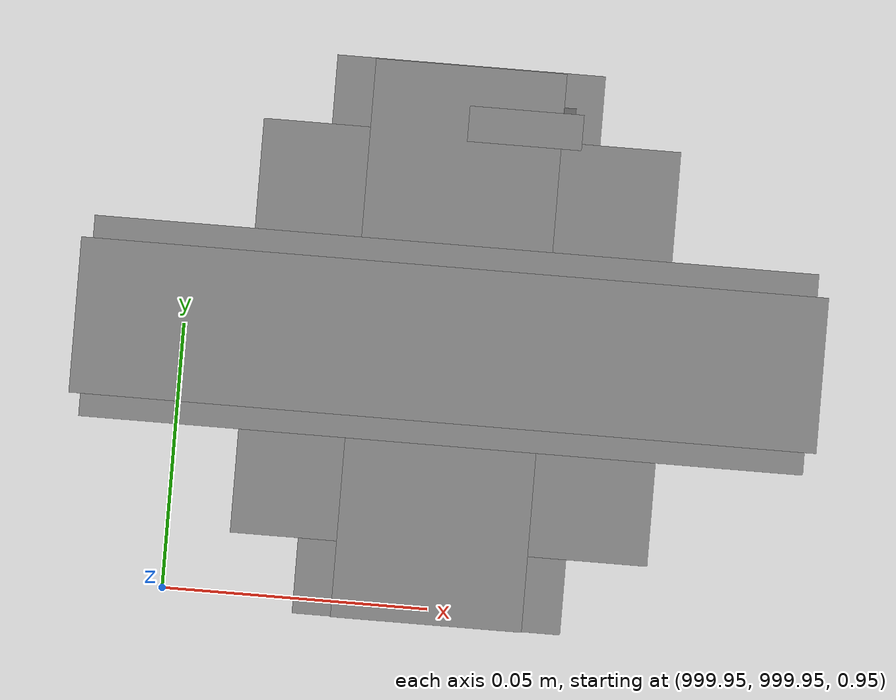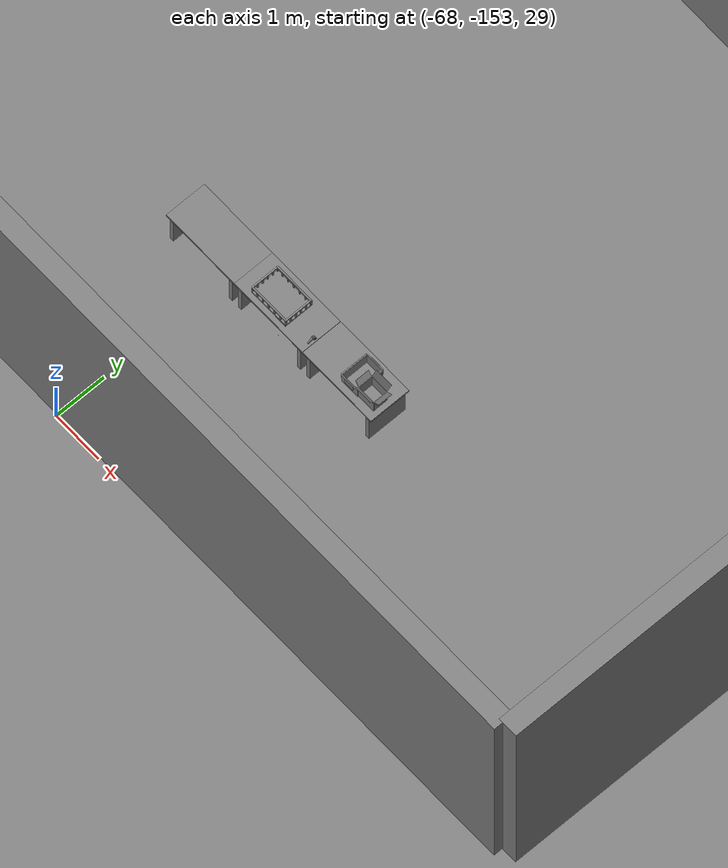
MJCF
<mujoco>
    <option gravity="0.000000000 0.000000000 -9.810000420" timestep="0.0049999999" integrator="implicitfast" density="1.225" viscosity="1.8000001e-05" noslip_iterations="10" iterations="100" sdf_iterations="50">
        <flag multiccd="disable"/>
    </option>
    <size memory="1000M"/>
    <compiler coordinate="local"/>
    <worldbody>
        <light cutoff="30" pos="0 1 1" dir="0 -1 -2"/>
        <light cutoff="30" pos="0 -1 1" dir="0 1 -2"/>
        <body pos="1000.000000000 1000.000000000 1.000000000" euler="0.000011953 0.000005123 -179.999984741" name="openloong_gripper_2f85_fix_base_usda_intel_box">
            <geom contype="1" conaffinity="1" density="1000" type="box" material="" rgba="0.500000000 0.500000000 0.500000000 1.000000000" solimp="0.899999976 0.949999988 0.001000000" friction="1.000000000 0.005000000 0.000100000" solref="0.020000000 1.000000000" margin="0" condim="3" group="0" pos="0.000000000 -0.000067139 0.000082284" quat="0.707106709 0.000000225 0.000000253 0.707106650" size="0.052800003 0.025300000 0.052800003" name="openloong_gripper_2f85_fix_base_usda_geom_C52E7E9D_F7B8_4B2A_8024_13D68AFA4301"/>
            <freejoint name="openloong_gripper_2f85_fix_base_usda_intel_box_joint"/>
            <site size="0.005000000 0.005000000 0.005000000" rgba="0.500000000 0.500000000 0.500000000 1.000000000" pos="0.000000000 0.000000000 0.000000000" quat="0.999961913 0.008726500 0.000000000 0.000000000" group="0" type="sphere" name="openloong_gripper_2f85_fix_base_usda_intel_boxsite"/>
        </body>
        <body pos="1000.000000000 1000.000000000 1.000000000" euler="0.000000000 0.000000000 180.000000000" name="openloong_gripper_2f85_fix_base_usda_wifi_box">
            <geom contype="1" conaffinity="1" density="1000" type="box" material="" rgba="0.500000000 0.500000000 0.500000000 1.000000000" solimp="0.899999976 0.949999988 0.001000000" friction="1.000000000 0.005000000 0.000100000" solref="0.020000000 1.000000000" margin="0" condim="3" group="0" pos="0.000000000 0.000000000 0.058978677" quat="0.000000000 0.000000047 0.000000000 1.000000000" size="0.068499997 0.018999999 0.059000000" name="openloong_gripper_2f85_fix_base_usda_geom_1754BD7B_2947_4B81_BCD7_346F6AF8863C"/>
            <freejoint name="openloong_gripper_2f85_fix_base_usda_wifi_box_joint"/>
            <site size="0.005000000 0.005000000 0.005000000" rgba="0.500000000 0.500000000 0.500000000 1.000000000" pos="0.000000000 0.000000000 0.000000000" quat="0.999961913 0.008726500 0.000000000 0.000000000" group="0" type="sphere" name="openloong_gripper_2f85_fix_base_usda_wifi_boxsite"/>
        </body>
        <body pos="-65.841133118 -149.045364380 31.169017792" euler="-173.706451416 -13.901082993 -24.949285507" mocap="true" name="spotlight5_SpotLight"/>
        <body pos="1000.000000000 999.999938965 1.000000000" euler="0.000000000 0.000000000 180.000000000" name="openloong_gripper_2f85_fix_base_usda_intelcore_i5">
            <geom contype="1" conaffinity="1" density="1000" type="box" material="" rgba="0.500000000 0.500000000 0.500000000 1.000000000" solimp="0.899999976 0.949999988 0.001000000" friction="1.000000000 0.005000000 0.000100000" solref="0.020000000 1.000000000" margin="0" condim="3" group="0" pos="0.000000000 0.000000000 0.051722717" quat="0.707106709 0.000000000 0.000000000 -0.707106769" size="0.052800000 0.018080002 0.052800000" name="openloong_gripper_2f85_fix_base_usda_geom_EF94EF2F_F287_4675_80F1_6F137693CB6B"/>
            <freejoint name="openloong_gripper_2f85_fix_base_usda_intelcore_i5_joint"/>
            <site size="0.005000000 0.005000000 0.005000000" rgba="0.500000000 0.500000000 0.500000000 1.000000000" pos="0.000000000 0.000000000 0.000000000" quat="0.999961913 0.008726534 0.000000000 0.000000000" group="0" type="sphere" name="openloong_gripper_2f85_fix_base_usda_intelcore_i5site"/>
        </body>
        <body pos="1000.000000000 1000.000000000 1.000000000" euler="0.000000000 0.000000000 180.000000000" name="openloong_gripper_2f85_fix_base_usda_cpu_fan">
            <geom contype="1" conaffinity="1" density="1000" type="box" material="" rgba="0.500000000 0.500000000 0.500000000 1.000000000" solimp="0.899999976 0.949999988 0.001000000" friction="1.000000000 0.005000000 0.000100000" solref="0.020000000 1.000000000" margin="0" condim="3" group="0" pos="0.000000000 0.000000000 0.070034981" quat="0.000000000 0.000000000 0.000000000 1.000000000" size="0.070700005 0.014699999 0.070700005" name="openloong_gripper_2f85_fix_base_usda_geom_3D4FFD08_ADE9_4B2C_8AD6_2687165D7ECB"/>
            <freejoint name="openloong_gripper_2f85_fix_base_usda_cpu_fan_joint"/>
            <site size="0.005000000 0.005000000 0.005000000" rgba="0.500000000 0.500000000 0.500000000 1.000000000" pos="0.000000000 0.000000000 0.000000000" quat="0.999961913 0.008726535 0.000000000 0.000000000" group="0" type="sphere" name="openloong_gripper_2f85_fix_base_usda_cpu_fancsite"/>
        </body>
        <body pos="-65.947402954 -148.951705933 31.166080475" euler="-42.257884979 -83.786415100 -33.176868439" mocap="true" name="spotlight3_SpotLight"/>
        <body pos="1000.000000000 1000.000000000 1.000000000" euler="0.000000000 0.000000000 180.000000000" name="openloong_gripper_2f85_fix_base_usda_battery_01">
            <geom contype="1" conaffinity="1" density="1000" type="box" material="" rgba="0.500000000 0.500000000 0.500000000 1.000000000" solimp="0.899999976 0.949999988 0.001000000" friction="1.000000000 0.005000000 0.000100000" solref="0.020000000 1.000000000" margin="0" condim="3" group="0" pos="-0.011123657 -0.041940309 0.101691343" quat="1.000000000 0.000000000 0.000000000 0.000000000" size="0.010800000 0.003375000 0.004725000" name="openloong_gripper_2f85_fix_base_usda_geom_1F5AD777_987B_43B3_860F_3C401E8617BD"/>
            <geom contype="1" conaffinity="1" density="1000" type="box" material="" rgba="0.500000000 0.500000000 0.500000000 1.000000000" solimp="0.899999976 0.949999988 0.001000000" friction="1.000000000 0.005000000 0.000100000" solref="0.020000000 1.000000000" margin="0" condim="3" group="0" pos="-0.010876465 -0.044247437 0.047066893" quat="0.998702705 -0.050920475 0.000000000 0.000000000" size="0.009450001 0.002700000 0.024975000" name="openloong_gripper_2f85_fix_base_usda_geom_611FB334_332E_4CAA_B74D_D611BE064D57"/>
            <geom contype="1" conaffinity="1" density="1000" type="box" material="" rgba="0.500000000 0.500000000 0.500000000 1.000000000" solimp="0.899999976 0.949999988 0.001000000" friction="1.000000000 0.005000000 0.000100000" solref="0.020000000 1.000000000" margin="0" condim="3" group="0" pos="-0.001235962 -0.000659180 0.047381196" quat="1.000000000 0.000000000 0.000000000 0.000000000" size="0.039420001 0.039150000 0.047250003" name="openloong_gripper_2f85_fix_base_usda_geom_415435CB_3985_45F4_8502_C4E1A9887A90"/>
            <geom contype="1" conaffinity="1" density="1000" type="box" material="" rgba="0.500000000 0.500000000 0.500000000 1.000000000" solimp="0.899999976 0.949999988 0.001000000" friction="1.000000000 0.005000000 0.000100000" solref="0.020000000 1.000000000" margin="0" condim="3" group="0" pos="-0.010876465 -0.039138794 0.009851727" quat="1.000000000 0.000000000 0.000000000 0.000000000" size="0.009450001 0.010800000 0.013500000" name="openloong_gripper_2f85_fix_base_usda_geom_D83357F4_A349_463E_B48B_B48B98853689"/>
            <geom contype="1" conaffinity="1" density="1000" type="box" material="" rgba="0.500000000 0.500000000 0.500000000 1.000000000" solimp="0.899999976 0.949999988 0.001000000" friction="1.000000000 0.005000000 0.000100000" solref="0.020000000 1.000000000" margin="0" condim="3" group="0" pos="-0.010876465 -0.041528322 0.071508206" quat="1.000000000 0.000000000 0.000000000 0.000000000" size="0.009450001 0.002700000 0.027000001" name="openloong_gripper_2f85_fix_base_usda_geom_0CD778FC_7D27_47EA_BDDC_9A6C26A1D53F"/>
            <freejoint name="openloong_gripper_2f85_fix_base_usda_battery_01_joint"/>
            <site size="0.005000000 0.005000000 0.005000000" rgba="0.500000000 0.500000000 0.500000000 1.000000000" pos="0.000000000 0.000000000 0.000000000" quat="0.999961913 0.008726500 0.000000000 0.000000000" group="0" type="sphere" name="openloong_gripper_2f85_fix_base_usda_battery_01site"/>
        </body>
        <body pos="-66.291000366 -149.099807739 31.166120529" euler="90.058967590 -1.876347423 137.069519043" mocap="true" name="spotlight4_SpotLight"/>
        <body pos="-64.866622925 -149.383972168 30.183746338" euler="89.999984741 89.999946594 0.000000000" name="openloong_gripper_2f85_fix_base_usda_bluebox_01">
            <geom contype="1" conaffinity="1" density="1000" type="box" material="" rgba="0.500000000 0.500000000 0.500000000 1.000000000" solimp="0.899999976 0.949999988 0.001000000" friction="1.000000000 0.005000000 0.000100000" solref="0.020000000 1.000000000" margin="0" condim="3" group="0" pos="0.276580811 0.187225342 0.000068665" quat="0.707106948 0.000077471 0.707106352 0.000077486" size="0.100000001 0.057999998 0.010000000" name="openloong_gripper_2f85_fix_base_usda_geom_7A0FF914_CC3C_49CC_911B_C6AF505C7A71"/>
            <geom contype="1" conaffinity="1" density="1000" type="box" material="" rgba="0.500000000 0.500000000 0.500000000 1.000000000" solimp="0.899999976 0.949999988 0.001000000" friction="1.000000000 0.005000000 0.000100000" solref="0.020000000 1.000000000" margin="0" condim="3" group="0" pos="0.000000000 0.002883911 0.000000000" quat="0.999999881 0.000000000 0.000000000 0.000000000" size="0.254000008 0.003000000 0.172000006" name="openloong_gripper_2f85_fix_base_usda_geom_FABBDCFF_490F_43A5_B8B0_14C73A511343"/>
            <geom contype="1" conaffinity="1" density="1000" type="box" material="" rgba="0.500000000 0.500000000 0.500000000 1.000000000" solimp="0.899999976 0.949999988 0.001000000" friction="1.000000000 0.005000000 0.000100000" solref="0.020000000 1.000000000" margin="0" condim="3" group="0" pos="0.000000000 0.124874115 0.173484802" quat="0.999796331 0.020176515 -0.000000015 0.000000030" size="0.259999990 0.119999997 0.007000000" name="openloong_gripper_2f85_fix_base_usda_geom_B24291EA_2B05_403B_AA82_C6391BCE27F0"/>
            <geom contype="1" conaffinity="1" density="1000" type="box" material="" rgba="0.500000000 0.500000000 0.500000000 1.000000000" solimp="0.899999976 0.949999988 0.001000000" friction="1.000000000 0.005000000 0.000100000" solref="0.020000000 1.000000000" margin="0" condim="3" group="0" pos="0.000000000 0.124874115 -0.173469543" quat="0.999796331 -0.020176545 -0.000000015 0.000000000" size="0.259999990 0.119999997 0.007000000" name="openloong_gripper_2f85_fix_base_usda_geom_02A77081_0DB7_4571_A5AD_C22C4F5489AE"/>
            <geom contype="1" conaffinity="1" density="1000" type="box" material="" rgba="0.500000000 0.500000000 0.500000000 1.000000000" solimp="0.899999976 0.949999988 0.001000000" friction="1.000000000 0.005000000 0.000100000" solref="0.020000000 1.000000000" margin="0" condim="3" group="0" pos="0.000000000 0.214008331 0.188980103" quat="0.999912977 0.013176724 0.000000015 0.000000000" size="0.259999990 0.029999999 0.012500000" name="openloong_gripper_2f85_fix_base_usda_geom_39007555_9ECD_4453_89D6_B38AC5C91986"/>
            <geom contype="1" conaffinity="1" density="1000" type="box" material="" rgba="0.500000000 0.500000000 0.500000000 1.000000000" solimp="0.899999976 0.949999988 0.001000000" friction="1.000000000 0.005000000 0.000100000" solref="0.020000000 1.000000000" margin="0" condim="3" group="0" pos="-0.258361816 0.125289917 0.001876831" quat="0.702796936 -0.020792112 0.710783124 0.020769298" size="0.189999998 0.119999997 0.009000000" name="openloong_gripper_2f85_fix_base_usda_geom_9FA13FE6_36CD_463A_BA87_C645FF026280"/>
            <geom contype="1" conaffinity="1" density="1000" type="box" material="" rgba="0.500000000 0.500000000 0.500000000 1.000000000" solimp="0.899999976 0.949999988 0.001000000" friction="1.000000000 0.005000000 0.000100000" solref="0.020000000 1.000000000" margin="0" condim="3" group="0" pos="0.000000000 0.214008331 -0.188980103" quat="0.999912977 -0.013176769 0.000000030 0.000000015" size="0.259999990 0.029999999 0.012500000" name="openloong_gripper_2f85_fix_base_usda_geom_F4E47747_F98E_4669_BAEE_044BFE4D6444"/>
            <geom contype="1" conaffinity="1" density="1000" type="box" material="" rgba="0.500000000 0.500000000 0.500000000 1.000000000" solimp="0.899999976 0.949999988 0.001000000" friction="1.000000000 0.005000000 0.000100000" solref="0.020000000 1.000000000" margin="0" condim="3" group="0" pos="-0.276611328 0.187225342 0.000068665" quat="0.707106650 0.000077441 0.707106709 0.000077456" size="0.100000001 0.057999998 0.010000000" name="openloong_gripper_2f85_fix_base_usda_geom_B5B059F7_F66A_4F83_8E58_65F307ECD04A"/>
            <geom contype="1" conaffinity="1" density="1000" type="box" material="" rgba="0.500000000 0.500000000 0.500000000 1.000000000" solimp="0.899999976 0.949999988 0.001000000" friction="1.000000000 0.005000000 0.000100000" solref="0.020000000 1.000000000" margin="0" condim="3" group="0" pos="0.258331299 0.125289917 0.001876831" quat="0.702851415 0.018856421 0.710823774 -0.019329369" size="0.189999998 0.119999997 0.009000000" name="openloong_gripper_2f85_fix_base_usda_geom_B18F97A1_D876_4CD8_8D63_72ADF1536E5B"/>
            <freejoint name="openloong_gripper_2f85_fix_base_usda_bluebox_01_joint"/>
            <site size="0.005000000 0.005000000 0.005000000" rgba="0.500000000 0.500000000 0.500000000 1.000000000" pos="0.000000000 0.000000000 0.000000000" quat="0.999961913 0.008726534 0.000000000 0.000000000" group="0" type="sphere" name="openloong_gripper_2f85_fix_base_usda_bluebox_01site"/>
        </body>
        <body pos="-64.496299744 -149.491867065 30.235729218" euler="0.000000000 0.000000000 89.999946594" name="openloong_gripper_2f85_fix_base_usda_cardboardbox_01">
            <geom contype="1" conaffinity="1" density="1000" type="box" material="" rgba="0.500000000 0.500000000 0.500000000 1.000000000" solimp="0.899999976 0.949999988 0.001000000" friction="1.000000000 0.005000000 0.000100000" solref="0.020000000 1.000000000" margin="0" condim="3" group="0" pos="-0.003166199 -0.004086494 0.005052090" quat="1.000000000 0.000000000 0.000000000 0.000000000" size="0.142499998 0.177500010 0.005000000" name="openloong_gripper_2f85_fix_base_usda_geom_3E64AA0E_389C_4A31_83F6_D64FDC9B2F6D"/>
            <geom contype="1" conaffinity="1" density="1000" type="box" material="" rgba="0.500000000 0.500000000 0.500000000 1.000000000" solimp="0.899999976 0.949999988 0.001000000" friction="1.000000000 0.005000000 0.000100000" solref="0.020000000 1.000000000" margin="0" condim="3" group="0" pos="-0.003166199 0.170316696 0.150570869" quat="1.000000000 0.000000000 0.000000000 0.000000000" size="0.142499998 0.005000000 0.149999991" name="openloong_gripper_2f85_fix_base_usda_geom_4A37D665_ACE6_46F2_BED4_B74F677B8663"/>
            <geom contype="1" conaffinity="1" density="1000" type="box" material="" rgba="0.500000000 0.500000000 0.500000000 1.000000000" solimp="0.899999976 0.949999988 0.001000000" friction="1.000000000 0.005000000 0.000100000" solref="0.020000000 1.000000000" margin="0" condim="3" group="0" pos="-0.147399902 -0.005307198 0.150570869" quat="1.000000000 0.000000000 0.000000000 0.000000000" size="0.005000000 0.177500010 0.149999991" name="openloong_gripper_2f85_fix_base_usda_geom_89736574_9F01_4FE5_8BC2_E6FFCDCEFA62"/>
            <geom contype="1" conaffinity="1" density="1000" type="box" material="" rgba="0.500000000 0.500000000 0.500000000 1.000000000" solimp="0.899999976 0.949999988 0.001000000" friction="1.000000000 0.005000000 0.000100000" solref="0.020000000 1.000000000" margin="0" condim="3" group="0" pos="0.140275955 -0.005307198 0.150570869" quat="1.000000000 0.000000000 0.000000000 0.000000000" size="0.005000000 0.177500010 0.149999991" name="openloong_gripper_2f85_fix_base_usda_geom_CF829CFC_24EB_436F_87C3_148A6560A551"/>
            <geom contype="1" conaffinity="1" density="1000" type="box" material="" rgba="0.500000000 0.500000000 0.500000000 1.000000000" solimp="0.899999976 0.949999988 0.001000000" friction="1.000000000 0.005000000 0.000100000" solref="0.020000000 1.000000000" margin="0" condim="3" group="0" pos="-0.003166199 -0.181550980 0.150570869" quat="1.000000000 0.000000000 0.000000000 0.000000000" size="0.142499998 0.005000000 0.149999991" name="openloong_gripper_2f85_fix_base_usda_geom_6B252537_1173_4BA3_AEB7_8D5C0E68DEDD"/>
            <freejoint name="openloong_gripper_2f85_fix_base_usda_cardboardbox_01_joint"/>
            <site size="0.005000000 0.005000000 0.005000000" rgba="0.500000000 0.500000000 0.500000000 1.000000000" pos="0.000000000 0.000000000 0.000000000" quat="0.999961913 0.008726535 0.000000000 0.000000000" group="0" type="sphere" name="openloong_gripper_2f85_fix_base_usda_site_91A6E591_1E74_4D68_AD58_30F543E674F1"/>
            <body pos="0.139160156 -0.004048347 0.301930904" euler="-179.999954224 49.383502960 179.999954224" name="openloong_gripper_2f85_fix_base_usda_A1_006">
                <geom contype="1" conaffinity="1" density="1000" type="box" material="" rgba="0.500000000 0.500000000 0.500000000 1.000000000" solimp="0.899999976 0.949999988 0.001000000" friction="1.000000000 0.005000000 0.000100000" solref="0.020000000 1.000000000" margin="0" condim="3" group="0" pos="-0.071587563 0.000009537 0.001745224" quat="0.999999881 0.000000000 0.000000000 0.000000000" size="0.071249999 0.179999992 0.002500000" name="openloong_gripper_2f85_fix_base_usda_geom_E8290FBA_F1E9_4F68_B9D0_B3B41C6296E7"/>
                <joint armature="0" stiffness="0.07" damping="0.0099999998" axis="0.000000 1.000000 0.000000" type="hinge" name="openloong_gripper_2f85_fix_base_usda_A1_006"/>
            </body>
            <body pos="-0.145902634 -0.004086494 0.301938057" euler="-180.000000000 -60.000011444 -180.000000000" name="openloong_gripper_2f85_fix_base_usda_A2_006">
                <geom contype="1" conaffinity="1" density="1000" type="box" material="" rgba="0.500000000 0.500000000 0.500000000 1.000000000" solimp="0.899999976 0.949999988 0.001000000" friction="1.000000000 0.005000000 0.000100000" solref="0.020000000 1.000000000" margin="0" condim="3" group="0" pos="0.071268082 0.000009537 0.002717972" quat="0.000002921 0.000000000 -0.000000030 0.999999881" size="0.071249999 0.179999992 0.002500000" name="openloong_gripper_2f85_fix_base_usda_geom_67D0A4D9_CA23_433C_9C75_47408B0C35DB"/>
                <joint armature="0" stiffness="0.07" damping="0.0099999998" axis="0.000000 1.000000 0.000000" type="hinge" name="openloong_gripper_2f85_fix_base_usda_A2_006"/>
            </body>
            <body pos="-0.003385544 0.175991058 0.301930904" euler="-125.858116150 -0.000004561 0.000002331" name="openloong_gripper_2f85_fix_base_usda_B2_006">
                <geom contype="1" conaffinity="1" density="1000" type="box" material="" rgba="0.500000000 0.500000000 0.500000000 1.000000000" solimp="0.899999976 0.949999988 0.001000000" friction="1.000000000 0.005000000 0.000100000" solref="0.020000000 1.000000000" margin="0" condim="3" group="0" pos="0.000009537 -0.070939064 -0.002470016" quat="0.999614120 0.027776197 -0.000000015 0.000000030" size="0.137500003 0.064999998 0.005000000" name="openloong_gripper_2f85_fix_base_usda_geom_C8454596_0D99_4461_A0DA_AD3867CAFD65"/>
                <joint armature="0" stiffness="0.07" damping="0.0099999998" axis="1.000000 0.000000 0.000000" type="hinge" name="openloong_gripper_2f85_fix_base_usda_B2_006"/>
            </body>
            <body pos="-0.003385544 -0.184140205 0.301938057" euler="147.805557251 0.000000000 0.000000000" name="openloong_gripper_2f85_fix_base_usda_B1_006">
                <geom contype="1" conaffinity="1" density="1000" type="box" material="" rgba="0.500000000 0.500000000 0.500000000 1.000000000" solimp="0.899999976 0.949999988 0.001000000" friction="1.000000000 0.005000000 0.000100000" solref="0.020000000 1.000000000" margin="0" condim="3" group="0" pos="-0.000028610 0.070202351 -0.002703667" quat="0.999614179 -0.027776167 0.000000000 0.000000000" size="0.137500003 0.064999998 0.005000000" name="openloong_gripper_2f85_fix_base_usda_geom_FD1CB435_4BE8_4EE4_83F0_1C2A7AD00A01"/>
                <joint armature="0" stiffness="0.07" damping="0.0099999998" axis="1.000000 0.000000 0.000000" type="hinge" name="openloong_gripper_2f85_fix_base_usda_B1_006"/>
            </body>
        </body>
        <body pos="-65.882858276 -149.481979370 30.229999542" euler="-64.487716675 0.000000000 0.000000000" name="openloong_gripper_2f85_fix_base_usda_Barcode">
            <geom contype="1" conaffinity="1" density="1000" type="box" material="" rgba="0.500000000 0.500000000 0.500000000 1.000000000" solimp="0.899999976 0.949999988 0.001000000" friction="1.000000000 0.005000000 0.000100000" solref="0.020000000 1.000000000" margin="0" condim="3" group="0" pos="0.000000000 0.013038635 0.001419067" quat="0.000000000 0.000000000 0.000000000 1.000000119" size="0.034000002 0.010000000 0.017999999" name="openloong_gripper_2f85_fix_base_usda_geom_4113E774_B096_4721_B4BE_8C6A435B6E5D"/>
            <geom contype="1" conaffinity="1" density="1000" type="box" material="" rgba="0.500000000 0.500000000 0.500000000 1.000000000" solimp="0.899999976 0.949999988 0.001000000" friction="1.000000000 0.005000000 0.000100000" solref="0.020000000 1.000000000" margin="0" condim="3" group="0" pos="0.000000000 -0.035301208 -0.007095337" quat="0.000000000 0.000000000 -0.043619365 0.999048233" size="0.028999999 0.010000000 0.020000000" name="openloong_gripper_2f85_fix_base_usda_geom_B7197E2C_1123_40AC_99B5_EB7C1C969BC9"/>
            <geom contype="1" conaffinity="1" density="1000" type="box" material="" rgba="0.500000000 0.500000000 0.500000000 1.000000000" solimp="0.899999976 0.949999988 0.001000000" friction="1.000000000 0.005000000 0.000100000" solref="0.020000000 1.000000000" margin="0" condim="3" group="0" pos="0.000000000 -0.043411255 -0.011749268" quat="0.922262907 0.386563420 0.000000000 0.000000000" size="0.026000001 0.010000000 0.020000000" name="openloong_gripper_2f85_fix_base_usda_geom_A06CD40B_6765_4B15_BB28_B432AA6BF473"/>
            <geom contype="1" conaffinity="1" density="1000" type="box" material="" rgba="0.500000000 0.500000000 0.500000000 1.000000000" solimp="0.899999976 0.949999988 0.001000000" friction="1.000000000 0.005000000 0.000100000" solref="0.020000000 1.000000000" margin="0" condim="3" group="0" pos="0.000000000 -0.016967773 -0.031860352" quat="0.000000000 0.000000000 0.000000000 1.000000119" size="0.008000000 0.010000000 0.013000000" name="openloong_gripper_2f85_fix_base_usda_geom_ADEED328_7244_4200_A362_70654CFBDDED"/>
            <geom contype="1" conaffinity="1" density="1000" type="box" material="" rgba="0.500000000 0.500000000 0.500000000 1.000000000" solimp="0.899999976 0.949999988 0.001000000" friction="1.000000000 0.005000000 0.000100000" solref="0.020000000 1.000000000" margin="0" condim="3" group="0" pos="0.000000000 -0.001869202 0.000312805" quat="0.953716993 0.300705761 0.000000000 0.000000000" size="0.032000002 0.010000000 0.018999999" name="openloong_gripper_2f85_fix_base_usda_geom_99F1D7BB_A7FC_4A1E_8862_0F718419787D"/>
            <geom contype="1" conaffinity="1" density="1000" type="box" material="" rgba="0.500000000 0.500000000 0.500000000 1.000000000" solimp="0.899999976 0.949999988 0.001000000" friction="1.000000000 0.005000000 0.000100000" solref="0.020000000 1.000000000" margin="0" condim="3" group="0" pos="0.000000000 -0.019531250 -0.003173828" quat="0.953716993 0.300705761 0.000000000 0.000000000" size="0.030999999 0.010000000 0.020000000" name="openloong_gripper_2f85_fix_base_usda_geom_DBA35E7B_DDE6_4E5E_ABC1_66AC379F707A"/>
            <geom contype="1" conaffinity="1" density="1000" type="box" material="" rgba="0.500000000 0.500000000 0.500000000 1.000000000" solimp="0.899999976 0.949999988 0.001000000" friction="1.000000000 0.005000000 0.000100000" solref="0.020000000 1.000000000" margin="0" condim="3" group="0" pos="0.000000000 -0.035301208 -0.007095337" quat="0.953716993 0.300705761 0.000000000 0.000000000" size="0.028999999 0.010000000 0.020000000" name="openloong_gripper_2f85_fix_base_usda_geom_70577DB9_B1F1_455C_89FB_C296EA34FDB3"/>
            <geom contype="1" conaffinity="1" density="1000" type="box" material="" rgba="0.500000000 0.500000000 0.500000000 1.000000000" solimp="0.899999976 0.949999988 0.001000000" friction="1.000000000 0.005000000 0.000100000" solref="0.020000000 1.000000000" margin="0" condim="3" group="0" pos="0.000000000 -0.042617798 -0.071121216" quat="0.000000000 0.000000000 0.000000000 1.000000119" size="0.013000000 0.021000000 0.059999999" name="openloong_gripper_2f85_fix_base_usda_geom_5D7AB805_A961_45DC_B55C_CA5CFBAE0F8B"/>
            <freejoint name="openloong_gripper_2f85_fix_base_usda_Barcode_joint"/>
            <site size="0.005000000 0.005000000 0.005000000" rgba="0.500000000 0.500000000 0.500000000 1.000000000" pos="0.000000000 0.000000000 0.000000000" quat="1.000000000 0.000000000 0.000000000 0.000000000" group="0" type="sphere" name="openloong_gripper_2f85_fix_base_usda_Barcode_site"/>
        </body>
        <body pos="-66.745018005 -149.392349243 30.184000015" euler="0.000000000 0.000000000 89.999946594" name="[22330054992664]_Basket_01">
            <geom contype="1" conaffinity="1" density="1000" type="box" material="" rgba="0.500000000 0.500000000 0.500000000 1.000000000" solimp="0.899999976 0.949999988 0.001000000" friction="1.000000000 0.005000000 0.000100000" solref="0.020000000 1.000000000" margin="0" condim="3" group="0" pos="-0.052425385 0.389207840 0.089787483" quat="0.707107008 0.000000000 0.000000000 0.707106411" size="0.014249999 0.014249999 0.059999999" name="[22330054992664]_geom_FBE82A46_2CC1_4714_A653_CBD59B743C49"/>
            <geom contype="1" conaffinity="1" density="1000" type="box" material="" rgba="0.500000000 0.500000000 0.500000000 1.000000000" solimp="0.899999976 0.949999988 0.001000000" friction="1.000000000 0.005000000 0.000100000" solref="0.020000000 1.000000000" margin="0" condim="3" group="0" pos="0.264015198 -0.133043289 0.089787483" quat="0.707107008 0.000000000 0.000000000 0.707106411" size="0.014249999 0.014249999 0.059999999" name="[22330054992664]_geom_5A7B867D_22BA_4EC9_A69C_A46F39216DD8"/>
            <geom contype="1" conaffinity="1" density="1000" type="box" material="" rgba="0.500000000 0.500000000 0.500000000 1.000000000" solimp="0.899999976 0.949999988 0.001000000" friction="1.000000000 0.005000000 0.000100000" solref="0.020000000 1.000000000" margin="0" condim="3" group="0" pos="-0.264015198 -0.265548706 0.089793205" quat="0.707107008 0.000000000 0.000000000 0.707106411" size="0.014249999 0.014249999 0.059999999" name="[22330054992664]_geom_E0EE2A62_0C74_458B_A360_95C0F01D99F9"/>
            <geom contype="1" conaffinity="1" density="1000" type="box" material="" rgba="0.500000000 0.500000000 0.500000000 1.000000000" solimp="0.899999976 0.949999988 0.001000000" friction="1.000000000 0.005000000 0.000100000" solref="0.020000000 1.000000000" margin="0" condim="3" group="0" pos="-0.160263062 -0.389322281 0.089793205" quat="0.707107008 0.000000000 0.000000000 0.707106411" size="0.014249999 0.014249999 0.059999999" name="[22330054992664]_geom_A458761A_A8FF_4071_8F87_99B405EFA1B1"/>
            <geom contype="1" conaffinity="1" density="1000" type="box" material="" rgba="0.500000000 0.500000000 0.500000000 1.000000000" solimp="0.899999976 0.949999988 0.001000000" friction="1.000000000 0.005000000 0.000100000" solref="0.020000000 1.000000000" margin="0" condim="3" group="0" pos="0.162265778 -0.389322281 0.089787483" quat="0.707107008 0.000000000 0.000000000 0.707106411" size="0.014249999 0.014249999 0.059999999" name="[22330054992664]_geom_20CD1777_577C_46E6_AE34_C86DFD03703F"/>
            <geom contype="1" conaffinity="1" density="1000" type="box" material="" rgba="0.500000000 0.500000000 0.500000000 1.000000000" solimp="0.899999976 0.949999988 0.001000000" friction="1.000000000 0.005000000 0.000100000" solref="0.020000000 1.000000000" margin="0" condim="3" group="0" pos="0.264015198 0.389207840 0.089787483" quat="0.707107008 0.000000000 0.000000000 0.707106411" size="0.014249999 0.014249999 0.059999999" name="[22330054992664]_geom_98EAD846_3514_4C2A_9370_AB6E7DF2616D"/>
            <geom contype="1" conaffinity="1" density="1000" type="box" material="" rgba="0.500000000 0.500000000 0.500000000 1.000000000" solimp="0.899999976 0.949999988 0.001000000" friction="1.000000000 0.005000000 0.000100000" solref="0.020000000 1.000000000" margin="0" condim="3" group="0" pos="-0.264015198 -0.133043289 0.089793205" quat="0.707107008 0.000000000 0.000000000 0.707106411" size="0.014249999 0.014249999 0.059999999" name="[22330054992664]_geom_F68548FC_79A5_4EBC_AC1C_0B2F2F3FFDFD"/>
            <geom contype="1" conaffinity="1" density="1000" type="box" material="" rgba="0.500000000 0.500000000 0.500000000 1.000000000" solimp="0.899999976 0.949999988 0.001000000" friction="1.000000000 0.005000000 0.000100000" solref="0.020000000 1.000000000" margin="0" condim="3" group="0" pos="-0.264026642 0.269256592 0.089793205" quat="0.707107008 0.000000000 0.000000000 0.707106411" size="0.014249999 0.014249999 0.059999999" name="[22330054992664]_geom_98452B7F_C755_4392_9919_45B10C18AC3C"/>
            <geom contype="1" conaffinity="1" density="1000" type="box" material="" rgba="0.500000000 0.500000000 0.500000000 1.000000000" solimp="0.899999976 0.949999988 0.001000000" friction="1.000000000 0.005000000 0.000100000" solref="0.020000000 1.000000000" margin="0" condim="3" group="0" pos="0.054462433 0.389207840 0.089787483" quat="0.707107008 0.000000000 0.000000000 0.707106411" size="0.014249999 0.014249999 0.059999999" name="[22330054992664]_geom_40848818_E143_4C1E_84A0_71B2009D1399"/>
            <geom contype="1" conaffinity="1" density="1000" type="box" material="" rgba="0.500000000 0.500000000 0.500000000 1.000000000" solimp="0.899999976 0.949999988 0.001000000" friction="1.000000000 0.005000000 0.000100000" solref="0.020000000 1.000000000" margin="0" condim="3" group="0" pos="0.054462433 -0.389322281 0.089787483" quat="0.707107008 0.000000000 0.000000000 0.707106411" size="0.014249999 0.014249999 0.059999999" name="[22330054992664]_geom_4F829E83_E6C1_4B31_8626_8D8F5133A40F"/>
            <geom contype="1" conaffinity="1" density="1000" type="box" material="" rgba="0.500000000 0.500000000 0.500000000 1.000000000" solimp="0.899999976 0.949999988 0.001000000" friction="1.000000000 0.005000000 0.000100000" solref="0.020000000 1.000000000" margin="0" condim="3" group="0" pos="0.264015198 0.269256592 0.089793205" quat="0.707107008 0.000000000 0.000000000 0.707106411" size="0.014249999 0.014249999 0.059999999" name="[22330054992664]_geom_68E74AA9_CF37_4342_9CD1_F014062C6F5B"/>
            <geom contype="1" conaffinity="1" density="1000" type="box" material="" rgba="0.500000000 0.500000000 0.500000000 1.000000000" solimp="0.899999976 0.949999988 0.001000000" friction="1.000000000 0.005000000 0.000100000" solref="0.020000000 1.000000000" margin="0" condim="3" group="0" pos="0.264015198 -0.389322281 0.089787483" quat="0.707107008 0.000000000 0.000000000 0.707106411" size="0.014249999 0.014249999 0.059999999" name="[22330054992664]_geom_233E3673_5BEC_45B7_96C2_51C79BBF38B9"/>
            <geom contype="1" conaffinity="1" density="1000" type="box" material="" rgba="0.500000000 0.500000000 0.500000000 1.000000000" solimp="0.899999976 0.949999988 0.001000000" friction="1.000000000 0.005000000 0.000100000" solref="0.020000000 1.000000000" margin="0" condim="3" group="0" pos="0.000000000 0.000000000 0.015998840" quat="0.707107008 0.000000000 0.000000000 0.707106411" size="0.403499991 0.279000014 0.015750000" name="[22330054992664]_geom_6FCEFEE9_6961_4BBB_9976_C14904653835"/>
            <geom contype="1" conaffinity="1" density="1000" type="box" material="" rgba="0.500000000 0.500000000 0.500000000 1.000000000" solimp="0.899999976 0.949999988 0.001000000" friction="1.000000000 0.005000000 0.000100000" solref="0.020000000 1.000000000" margin="0" condim="3" group="0" pos="0.000000000 -0.389476776 0.163619041" quat="0.707107008 0.000000000 0.000000000 0.707106411" size="0.015000000 0.277500004 0.015750000" name="[22330054992664]_geom_94E4AF87_D087_4791_9A04_319C04970B0B"/>
            <geom contype="1" conaffinity="1" density="1000" type="box" material="" rgba="0.500000000 0.500000000 0.500000000 1.000000000" solimp="0.899999976 0.949999988 0.001000000" friction="1.000000000 0.005000000 0.000100000" solref="0.020000000 1.000000000" margin="0" condim="3" group="0" pos="0.162265778 0.389207840 0.089787483" quat="0.707107008 0.000000000 0.000000000 0.707106411" size="0.014249999 0.014249999 0.059999999" name="[22330054992664]_geom_506FC859_193E_4BB1_B7FC_C365566833DD"/>
            <geom contype="1" conaffinity="1" density="1000" type="box" material="" rgba="0.500000000 0.500000000 0.500000000 1.000000000" solimp="0.899999976 0.949999988 0.001000000" friction="1.000000000 0.005000000 0.000100000" solref="0.020000000 1.000000000" margin="0" condim="3" group="0" pos="0.000000000 0.389471054 0.163619041" quat="0.707107008 0.000000000 0.000000000 0.707106411" size="0.015000000 0.277500004 0.015750000" name="[22330054992664]_geom_523CC19A_8924_4C44_A8F7_35A4C017C7D6"/>
            <geom contype="1" conaffinity="1" density="1000" type="box" material="" rgba="0.500000000 0.500000000 0.500000000 1.000000000" solimp="0.899999976 0.949999988 0.001000000" friction="1.000000000 0.005000000 0.000100000" solref="0.020000000 1.000000000" margin="0" condim="3" group="0" pos="-0.263511658 0.000000000 0.163619041" quat="0.707107008 0.000000000 0.000000000 0.707106411" size="0.403499991 0.015000000 0.015750000" name="[22330054992664]_geom_1956297F_FC46_4F47_96A5_0692F6879D15"/>
            <geom contype="1" conaffinity="1" density="1000" type="box" material="" rgba="0.500000000 0.500000000 0.500000000 1.000000000" solimp="0.899999976 0.949999988 0.001000000" friction="1.000000000 0.005000000 0.000100000" solref="0.020000000 1.000000000" margin="0" condim="3" group="0" pos="-0.264015198 0.141334534 0.089793205" quat="0.707107008 0.000000000 0.000000000 0.707106411" size="0.014249999 0.014249999 0.059999999" name="[22330054992664]_geom_35382F33_7FBC_4D59_98FD_1616310351F2"/>
            <geom contype="1" conaffinity="1" density="1000" type="box" material="" rgba="0.500000000 0.500000000 0.500000000 1.000000000" solimp="0.899999976 0.949999988 0.001000000" friction="1.000000000 0.005000000 0.000100000" solref="0.020000000 1.000000000" margin="0" condim="3" group="0" pos="0.264015198 -0.265548706 0.089787483" quat="0.707107008 0.000000000 0.000000000 0.707106411" size="0.014249999 0.014249999 0.059999999" name="[22330054992664]_geom_BA38EC76_0EDC_4949_8B22_BFDC38C9D3CC"/>
            <geom contype="1" conaffinity="1" density="1000" type="box" material="" rgba="0.500000000 0.500000000 0.500000000 1.000000000" solimp="0.899999976 0.949999988 0.001000000" friction="1.000000000 0.005000000 0.000100000" solref="0.020000000 1.000000000" margin="0" condim="3" group="0" pos="-0.160263062 0.389207840 0.089787483" quat="0.707107008 0.000000000 0.000000000 0.707106411" size="0.014249999 0.014249999 0.059999999" name="[22330054992664]_geom_09619040_18B7_4869_AFAC_2F56A34438C3"/>
            <geom contype="1" conaffinity="1" density="1000" type="box" material="" rgba="0.500000000 0.500000000 0.500000000 1.000000000" solimp="0.899999976 0.949999988 0.001000000" friction="1.000000000 0.005000000 0.000100000" solref="0.020000000 1.000000000" margin="0" condim="3" group="0" pos="-0.052425385 -0.389322281 0.089787483" quat="0.707107008 0.000000000 0.000000000 0.707106411" size="0.014249999 0.014249999 0.059999999" name="[22330054992664]_geom_20943B17_3E1C_4C87_940E_3AA58F05AD16"/>
            <geom contype="1" conaffinity="1" density="1000" type="box" material="" rgba="0.500000000 0.500000000 0.500000000 1.000000000" solimp="0.899999976 0.949999988 0.001000000" friction="1.000000000 0.005000000 0.000100000" solref="0.020000000 1.000000000" margin="0" condim="3" group="0" pos="-0.264026642 -0.389322281 0.089793205" quat="0.707107008 0.000000000 0.000000000 0.707106411" size="0.014249999 0.014249999 0.059999999" name="[22330054992664]_geom_4FC77AE5_B1AF_4501_8E8E_99570DA003C4"/>
            <geom contype="1" conaffinity="1" density="1000" type="box" material="" rgba="0.500000000 0.500000000 0.500000000 1.000000000" solimp="0.899999976 0.949999988 0.001000000" friction="1.000000000 0.005000000 0.000100000" solref="0.020000000 1.000000000" margin="0" condim="3" group="0" pos="0.264015198 0.141334534 0.089787483" quat="0.707107008 0.000000000 0.000000000 0.707106411" size="0.014249999 0.014249999 0.059999999" name="[22330054992664]_geom_CA5EC510_5FE1_45D9_A89A_DDB7D09A6130"/>
            <geom contype="1" conaffinity="1" density="1000" type="box" material="" rgba="0.500000000 0.500000000 0.500000000 1.000000000" solimp="0.899999976 0.949999988 0.001000000" friction="1.000000000 0.005000000 0.000100000" solref="0.020000000 1.000000000" margin="0" condim="3" group="0" pos="-0.264015198 0.389207840 0.089793205" quat="0.707107008 0.000000000 0.000000000 0.707106411" size="0.014249999 0.014249999 0.059999999" name="[22330054992664]_geom_758709CF_758C_40DA_8997_85D3FE355F79"/>
            <geom contype="1" conaffinity="1" density="1000" type="box" material="" rgba="0.500000000 0.500000000 0.500000000 1.000000000" solimp="0.899999976 0.949999988 0.001000000" friction="1.000000000 0.005000000 0.000100000" solref="0.020000000 1.000000000" margin="0" condim="3" group="0" pos="0.264015198 0.004480362 0.089787483" quat="0.707107008 0.000000000 0.000000000 0.707106411" size="0.014249999 0.014249999 0.059999999" name="[22330054992664]_geom_98DE7E3E_2203_4984_9E00_C43253E85C84"/>
            <geom contype="1" conaffinity="1" density="1000" type="box" material="" rgba="0.500000000 0.500000000 0.500000000 1.000000000" solimp="0.899999976 0.949999988 0.001000000" friction="1.000000000 0.005000000 0.000100000" solref="0.020000000 1.000000000" margin="0" condim="3" group="0" pos="0.263694763 -0.000011444 0.163619041" quat="0.707107008 0.000000000 0.000000000 0.707106411" size="0.403499991 0.015000000 0.015750000" name="[22330054992664]_geom_2521D51A_2B2D_43B5_9EA5_51535CF3996F"/>
            <geom contype="1" conaffinity="1" density="1000" type="box" material="" rgba="0.500000000 0.500000000 0.500000000 1.000000000" solimp="0.899999976 0.949999988 0.001000000" friction="1.000000000 0.005000000 0.000100000" solref="0.020000000 1.000000000" margin="0" condim="3" group="0" pos="-0.264015198 0.004480362 0.089793205" quat="0.707107008 0.000000000 0.000000000 0.707106411" size="0.014249999 0.014249999 0.059999999" name="[22330054992664]_geom_3A7D3727_0E49_4F71_80B9_44C3BA695443"/>
            <freejoint name="[22330054992664]_joint_4627A95E_C0D7_4876_9F75_0C33AEEB9EA5"/>
        </body>
        <body pos="0.000000000 0.000000000 0.000000000" euler="0.000000000 0.000000000 0.000000000" name="Static Objects_Static Objects">
            <geom contype="1" conaffinity="1" density="1000" type="box" material="" rgba="0.500000000 0.500000000 0.500000000 1.000000000" solimp="0.899999976 0.949999988 0.001000000" friction="1.000000000 0.005000000 0.000100000" solref="0.020000000 1.000000000" margin="0" condim="3" group="0" pos="-67.544113159 -149.365814209 29.727830887" quat="0.500000417 0.499999970 0.499999553 0.499999970" size="0.381000012 0.319999993 0.041000001" name="Static Objects_geom_8D418F1F_8416_4C00_908A_CD139CFEA7F8"/>
            <geom contype="1" conaffinity="1" density="1000" type="box" material="" rgba="0.500000000 0.500000000 0.500000000 1.000000000" solimp="0.899999976 0.949999988 0.001000000" friction="1.000000000 0.005000000 0.000100000" solref="0.020000000 1.000000000" margin="0" condim="3" group="0" pos="-68.239501953 -149.365814209 30.086868286" quat="0.500000417 0.499999970 0.499999553 0.499999970" size="0.370999992 0.039500002 0.745000005" name="Static Objects_geom_099C0128_530D_4C17_9034_2BE71494345B"/>
            <geom contype="1" conaffinity="1" density="1000" type="box" material="" rgba="0.500000000 0.500000000 0.500000000 1.000000000" solimp="0.899999976 0.949999988 0.001000000" friction="1.000000000 0.005000000 0.000100000" solref="0.020000000 1.000000000" margin="0" condim="3" group="0" pos="-68.239501953 -149.365814209 30.147235870" quat="0.500000417 0.499999970 0.499999553 0.499999970" size="0.400000006 0.022000000 0.800000012" name="Static Objects_geom_7189C0E8_4FCD_4D4B_BEBB_FE1686EF1E31"/>
            <geom contype="1" conaffinity="1" density="1000" type="box" material="" rgba="0.500000000 0.500000000 0.500000000 1.000000000" solimp="0.899999976 0.949999988 0.001000000" friction="1.000000000 0.005000000 0.000100000" solref="0.020000000 1.000000000" margin="0" condim="3" group="0" pos="-68.934890747 -149.365814209 29.727830887" quat="0.500000417 0.499999970 0.499999553 0.499999970" size="0.381000012 0.319999993 0.041000001" name="Static Objects_geom_F2584242_A676_49E2_8E6B_B59538F96570"/>
            <geom contype="1" conaffinity="1" density="1000" type="box" material="" rgba="0.500000000 0.500000000 0.500000000 1.000000000" solimp="0.899999976 0.949999988 0.001000000" friction="1.000000000 0.005000000 0.000100000" solref="0.020000000 1.000000000" margin="0" condim="3" group="0" pos="-68.239501953 -149.365814209 29.561563492" quat="0.500000417 0.499999970 0.499999553 0.499999970" size="0.020000000 0.022000000 0.660000026" name="Static Objects_geom_F34D420A_4801_480E_80C6_F5F45CFFDCDB"/>
            <geom contype="1" conaffinity="1" density="1000" type="box" material="" rgba="0.500000000 0.500000000 0.500000000 1.000000000" solimp="0.899999976 0.949999988 0.001000000" friction="1.000000000 0.005000000 0.000100000" solref="0.020000000 1.000000000" margin="0" condim="3" group="0" pos="-65.945671082 -149.365814209 29.727830887" quat="0.500000417 0.499999970 0.499999553 0.499999970" size="0.381000012 0.319999993 0.041000001" name="Static Objects_geom_243ECFC1_5358_42DF_8139_DCC0B751403A"/>
            <geom contype="1" conaffinity="1" density="1000" type="box" material="" rgba="0.500000000 0.500000000 0.500000000 1.000000000" solimp="0.899999976 0.949999988 0.001000000" friction="1.000000000 0.005000000 0.000100000" solref="0.020000000 1.000000000" margin="0" condim="3" group="0" pos="-66.641059875 -149.365814209 30.086868286" quat="0.500000417 0.499999970 0.499999553 0.499999970" size="0.370999992 0.039500002 0.745000005" name="Static Objects_geom_A85B24C4_E53A_4C7D_B03B_D6819B0F3CC5"/>
            <geom contype="1" conaffinity="1" density="1000" type="box" material="" rgba="0.500000000 0.500000000 0.500000000 1.000000000" solimp="0.899999976 0.949999988 0.001000000" friction="1.000000000 0.005000000 0.000100000" solref="0.020000000 1.000000000" margin="0" condim="3" group="0" pos="-66.641059875 -149.365814209 30.147235870" quat="0.500000417 0.499999970 0.499999553 0.499999970" size="0.400000006 0.022000000 0.800000012" name="Static Objects_geom_A80A0589_E2EE_468A_A601_7354CDCA94E1"/>
            <geom contype="1" conaffinity="1" density="1000" type="box" material="" rgba="0.500000000 0.500000000 0.500000000 1.000000000" solimp="0.899999976 0.949999988 0.001000000" friction="1.000000000 0.005000000 0.000100000" solref="0.020000000 1.000000000" margin="0" condim="3" group="0" pos="-67.336448669 -149.365814209 29.727830887" quat="0.500000417 0.499999970 0.499999553 0.499999970" size="0.381000012 0.319999993 0.041000001" name="Static Objects_geom_8A2C57EE_A232_4940_A381_F944D9166E19"/>
            <geom contype="1" conaffinity="1" density="1000" type="box" material="" rgba="0.500000000 0.500000000 0.500000000 1.000000000" solimp="0.899999976 0.949999988 0.001000000" friction="1.000000000 0.005000000 0.000100000" solref="0.020000000 1.000000000" margin="0" condim="3" group="0" pos="-66.641059875 -149.365814209 29.561563492" quat="0.500000417 0.499999970 0.499999553 0.499999970" size="0.020000000 0.022000000 0.660000026" name="Static Objects_geom_6A377873_56AF_427E_A030_FCBFF15708B1"/>
            <geom contype="1" conaffinity="1" density="1000" type="box" material="" rgba="0.500000000 0.500000000 0.500000000 1.000000000" solimp="0.899999976 0.949999988 0.001000000" friction="1.000000000 0.005000000 0.000100000" solref="0.020000000 1.000000000" margin="0" condim="3" group="0" pos="-64.338577271 -149.365814209 29.727830887" quat="0.500000417 0.499999970 0.499999553 0.499999970" size="0.381000012 0.319999993 0.041000001" name="Static Objects_geom_67742C3C_875D_4698_80ED_2686893DBB20"/>
            <geom contype="1" conaffinity="1" density="1000" type="box" material="" rgba="0.500000000 0.500000000 0.500000000 1.000000000" solimp="0.899999976 0.949999988 0.001000000" friction="1.000000000 0.005000000 0.000100000" solref="0.020000000 1.000000000" margin="0" condim="3" group="0" pos="-65.033966064 -149.365814209 30.086868286" quat="0.500000417 0.499999970 0.499999553 0.499999970" size="0.370999992 0.039500002 0.745000005" name="Static Objects_geom_0ABB11F5_BBBA_4D5B_B89E_690812B17F1B"/>
            <geom contype="1" conaffinity="1" density="1000" type="box" material="" rgba="0.500000000 0.500000000 0.500000000 1.000000000" solimp="0.899999976 0.949999988 0.001000000" friction="1.000000000 0.005000000 0.000100000" solref="0.020000000 1.000000000" margin="0" condim="3" group="0" pos="-65.033966064 -149.365814209 30.147235870" quat="0.500000417 0.499999970 0.499999553 0.499999970" size="0.400000006 0.022000000 0.800000012" name="Static Objects_geom_9C19FA4A_6B7D_446F_9CA9_055F777D8053"/>
            <geom contype="1" conaffinity="1" density="1000" type="box" material="" rgba="0.500000000 0.500000000 0.500000000 1.000000000" solimp="0.899999976 0.949999988 0.001000000" friction="1.000000000 0.005000000 0.000100000" solref="0.020000000 1.000000000" margin="0" condim="3" group="0" pos="-65.729354858 -149.365814209 29.727830887" quat="0.500000417 0.499999970 0.499999553 0.499999970" size="0.381000012 0.319999993 0.041000001" name="Static Objects_geom_97A07C21_FCC0_4B2E_87D4_9EE2A2065CBC"/>
            <geom contype="1" conaffinity="1" density="1000" type="box" material="" rgba="0.500000000 0.500000000 0.500000000 1.000000000" solimp="0.899999976 0.949999988 0.001000000" friction="1.000000000 0.005000000 0.000100000" solref="0.020000000 1.000000000" margin="0" condim="3" group="0" pos="-65.033966064 -149.365814209 29.561563492" quat="0.500000417 0.499999970 0.499999553 0.499999970" size="0.020000000 0.022000000 0.660000026" name="Static Objects_geom_743EC592_BCCD_4E75_BFA5_7DC0A552BAB1"/>
            <geom contype="1" conaffinity="1" density="1000" type="box" material="" rgba="0.500000000 0.500000000 0.500000000 1.000000000" solimp="0.899999976 0.949999988 0.001000000" friction="1.000000000 0.005000000 0.000100000" solref="0.020000000 1.000000000" margin="0" condim="3" group="0" pos="-61.754566193 -137.853729248 33.906845093" quat="0.707107067 0.000000000 0.000000000 0.707106471" size="0.759999990 0.759999990 4.500000000" name="Static Objects_geom_2C2731AC_3B94_4CD8_95F7_CDBD053B96E4"/>
            <geom contype="1" conaffinity="1" density="1000" type="box" material="" rgba="0.500000000 0.500000000 0.500000000 1.000000000" solimp="0.899999976 0.949999988 0.001000000" friction="1.000000000 0.005000000 0.000100000" solref="0.020000000 1.000000000" margin="0" condim="3" group="0" pos="-57.511135101 -144.927108765 31.707921982" quat="1.000000000 0.000000000 0.000000000 0.000000000" size="0.200000003 8.000000000 2.299999952" name="Static Objects_geom_8BA8B97A_B0DC_4BEA_B225_9C48CF288775"/>
            <geom contype="1" conaffinity="1" density="1000" type="box" material="" rgba="0.500000000 0.500000000 0.500000000 1.000000000" solimp="0.899999976 0.949999988 0.001000000" friction="1.000000000 0.005000000 0.000100000" solref="0.020000000 1.000000000" margin="0" condim="3" group="0" pos="-80.517646790 -157.574050903 31.688196182" quat="0.707107067 0.000000000 0.000000000 0.707106471" size="0.600000024 0.600000024 2.299999952" name="Static Objects_geom_3E25F4C2_7727_4F0C_9D28_DD658790A87D"/>
            <geom contype="1" conaffinity="1" density="1000" type="box" material="" rgba="0.500000000 0.500000000 0.500000000 1.000000000" solimp="0.899999976 0.949999988 0.001000000" friction="1.000000000 0.005000000 0.000100000" solref="0.020000000 1.000000000" margin="0" condim="3" group="0" pos="-80.711044312 -147.414932251 31.666158676" quat="1.000000000 0.000000000 0.000000000 0.000000000" size="0.200000003 10.000000000 2.299999952" name="Static Objects_geom_7BC127AC_AC6A_4D29_9BAC_580E26FA5A63"/>
            <geom contype="1" conaffinity="1" density="1000" type="box" material="" rgba="0.500000000 0.500000000 0.500000000 1.000000000" solimp="0.899999976 0.949999988 0.001000000" friction="1.000000000 0.005000000 0.000100000" solref="0.020000000 1.000000000" margin="0" condim="3" group="0" pos="-57.687217712 -137.434692383 31.688196182" quat="0.707107067 0.000000000 0.000000000 0.707106471" size="0.600000024 0.600000024 2.299999952" name="Static Objects_geom_4A40C975_7214_4992_9201_14E8B2FFAC00"/>
            <geom contype="1" conaffinity="1" density="1000" type="box" material="" rgba="0.500000000 0.500000000 0.500000000 1.000000000" solimp="0.899999976 0.949999988 0.001000000" friction="1.000000000 0.005000000 0.000100000" solref="0.020000000 1.000000000" margin="0" condim="3" group="0" pos="-69.537033081 -140.263229370 31.714921951" quat="0.707107067 0.000000000 0.000000000 0.707106471" size="0.759999990 4.500000000 2.299999952" name="Static Objects_geom_4E8C9094_8672_4908_90FE_187EC1FBFBED"/>
            <geom contype="1" conaffinity="1" density="1000" type="box" material="" rgba="0.500000000 0.500000000 0.500000000 1.000000000" solimp="0.899999976 0.949999988 0.001000000" friction="1.000000000 0.005000000 0.000100000" solref="0.020000000 1.000000000" margin="0" condim="3" group="0" pos="-80.073638916 -137.853713989 33.906845093" quat="0.707107067 0.000000000 0.000000000 0.707106471" size="0.759999990 0.759999990 4.500000000" name="Static Objects_geom_8C1874BD_7224_470C_A390_FEB2B1812D86"/>
            <geom contype="1" conaffinity="1" density="1000" type="box" material="" rgba="0.500000000 0.500000000 0.500000000 1.000000000" solimp="0.899999976 0.949999988 0.001000000" friction="1.000000000 0.005000000 0.000100000" solref="0.020000000 1.000000000" margin="0" condim="3" group="0" pos="-73.406707764 -155.734664917 31.707921982" quat="1.000000000 0.000000000 0.000000000 0.000000000" size="0.200000003 3.000000000 2.299999952" name="Static Objects_geom_5C593465_7CC9_4B0F_A300_82B6C00144CD"/>
            <geom contype="1" conaffinity="1" density="1000" type="box" material="" rgba="0.500000000 0.500000000 0.500000000 1.000000000" solimp="0.899999976 0.949999988 0.001000000" friction="1.000000000 0.005000000 0.000100000" solref="0.020000000 1.000000000" margin="0" condim="3" group="0" pos="-68.497543335 -137.448257446 31.707921982" quat="0.707107067 0.000000000 0.000000000 0.707106471" size="0.200000003 14.000000000 2.299999952" name="Static Objects_geom_5A4126A8_0B4C_4275_9C1D_FA9D15BF5934"/>
            <geom contype="1" conaffinity="1" density="1000" type="cylinder" material="" rgba="0.500000000 0.500000000 0.500000000 1.000000000" solimp="0.899999976 0.949999988 0.001000000" friction="1.000000000 0.005000000 0.000100000" solref="0.020000000 1.000000000" margin="0" condim="3" group="0" pos="-68.868522644 -142.134506226 31.711090088" quat="0.707107067 0.000000000 0.000000000 0.707106471" size="0.509999990 2.299999952 1.000000000" name="Static Objects_geom_62E9ADE7_8AD8_4426_BB66_5F2CD6BEA698"/>
            <geom contype="1" conaffinity="1" density="1000" type="plane" material="" rgba="0.500000000 0.500000000 0.500000000 1.000000000" solimp="0.899999976 0.949999988 0.001000000" friction="1.000000000 0.005000000 0.000100000" solref="0.020000000 1.000000000" margin="0" condim="3" group="0" pos="-72.873703003 -147.131927490 29.409669876" quat="1.000000000 0.000000000 0.000000000 0.000000000" size="18.000000000 14.000000000 1.000000000" name="Static Objects_geom_11347CA6_C231_4CA5_ACB1_E8B6E491D5FE"/>
            <geom contype="1" conaffinity="1" density="1000" type="box" material="" rgba="0.500000000 0.500000000 0.500000000 1.000000000" solimp="0.899999976 0.949999988 0.001000000" friction="1.000000000 0.005000000 0.000100000" solref="0.020000000 1.000000000" margin="0" condim="3" group="0" pos="-79.943580627 -157.782272339 31.707921982" quat="0.707107067 0.000000000 0.000000000 0.707106471" size="0.200000003 7.000000000 2.299999952" name="Static Objects_geom_C92E60E8_EA12_40B2_8DD2_D6EB7E8A76EA"/>
            <geom contype="1" conaffinity="1" density="1000" type="box" material="" rgba="0.500000000 0.500000000 0.500000000 1.000000000" solimp="0.899999976 0.949999988 0.001000000" friction="1.000000000 0.005000000 0.000100000" solref="0.020000000 1.000000000" margin="0" condim="3" group="0" pos="-65.421028137 -152.903442383 31.707921982" quat="0.707107067 0.000000000 0.000000000 0.707106471" size="0.200000003 7.800000191 2.299999952" name="Static Objects_geom_06F2949D_2F85_4CFC_A93B_57FF096B4561"/>
            <geom contype="1" conaffinity="1" density="1000" type="box" material="" rgba="0.500000000 0.500000000 0.500000000 1.000000000" solimp="0.899999976 0.949999988 0.001000000" friction="1.000000000 0.005000000 0.000100000" solref="0.020000000 1.000000000" margin="0" condim="3" group="0" pos="-74.776908875 -149.964416504 31.688196182" quat="1.000000000 0.000000000 0.000000000 0.000000000" size="0.600000024 0.409999996 2.299999952" name="Static Objects_geom_56C8F902_AC33_48F5_93B5_3B5676C66A1F"/>
            <geom contype="1" conaffinity="1" density="1000" type="cylinder" material="" rgba="0.500000000 0.500000000 0.500000000 1.000000000" solimp="0.899999976 0.949999988 0.001000000" friction="1.000000000 0.005000000 0.000100000" solref="0.020000000 1.000000000" margin="0" condim="3" group="0" pos="-60.161884308 -142.134506226 31.711090088" quat="0.707107067 0.000000000 0.000000000 0.707106471" size="0.509999990 2.299999952 1.000000000" name="Static Objects_geom_A579194C_71DA_4D63_95D7_2A63CBC52DA5"/>
            <geom contype="1" conaffinity="1" density="1000" type="cylinder" material="" rgba="0.500000000 0.500000000 0.500000000 1.000000000" solimp="0.899999976 0.949999988 0.001000000" friction="1.000000000 0.005000000 0.000100000" solref="0.020000000 1.000000000" margin="0" condim="3" group="0" pos="-75.382453918 -149.963455200 31.711090088" quat="0.707107067 0.000000000 0.000000000 0.707106471" size="0.409999996 2.299999952 1.000000000" name="Static Objects_geom_9D0193CE_659D_4C61_89EF_270562742174"/>
            <geom contype="1" conaffinity="1" density="1000" type="cylinder" material="" rgba="0.500000000 0.500000000 0.500000000 1.000000000" solimp="0.899999976 0.949999988 0.001000000" friction="1.000000000 0.005000000 0.000100000" solref="0.020000000 1.000000000" margin="0" condim="3" group="0" pos="-74.154960632 -149.963455200 31.711090088" quat="0.707107067 0.000000000 0.000000000 0.707106471" size="0.409999996 2.299999952 1.000000000" name="Static Objects_geom_7DC77E49_9930_4B1B_905A_6E323123673F"/>
            <geom contype="1" conaffinity="1" density="1000" type="cylinder" material="" rgba="0.500000000 0.500000000 0.500000000 1.000000000" solimp="0.899999976 0.949999988 0.001000000" friction="1.000000000 0.005000000 0.000100000" solref="0.020000000 1.000000000" margin="0" condim="3" group="0" pos="-77.566612244 -142.134506226 31.711090088" quat="0.707107067 0.000000000 0.000000000 0.707106471" size="0.509999990 2.299999952 1.000000000" name="Static Objects_geom_26B52952_4FD0_4238_A387_022D68D351B9"/>
        </body>
        <body pos="-66.291030884 -149.869689941 29.018842697" euler="0.000000000 0.000000000 89.999946594" mocap="true" name="openloong_gripper_2f85_fix_base_usda_leftHandMocap"/>
        <body pos="-66.291030884 -149.869689941 29.018842697" euler="0.000000000 0.000000000 89.999946594" mocap="true" name="openloong_gripper_2f85_fix_base_usda_rightHandMocap"/>
        <body pos="-66.291030884 -149.869689941 30.218843460" euler="0.000000000 0.000000000 89.999946594" name="openloong_gripper_2f85_fix_base_usda_base_link">
            <geom contype="1" conaffinity="1" density="1000" type="mesh" material="" rgba="0.783999979 0.783999979 0.783999979 1.000000000" solimp="0.899999976 0.949999988 0.001000000" friction="1.000000000 0.005000000 0.000100000" solref="0.020000000 1.000000000" margin="0" condim="3" group="3" mesh="base_link" pos="0.000000000 0.000000000 0.000000000" quat="1.000000000 0.000000000 0.000000000 0.000000000" size="1.000000000 1.000000000 1.000000000" name="openloong_gripper_2f85_fix_base_usda__geom_7_9092B55D_B0E5_42C6_89BE_219400261CDD"/>
            <site size="0.005000000 0.005000000 0.005000000" rgba="0.500000000 0.500000000 0.500000000 1.000000000" pos="0.000000000 0.000000000 0.000000000" quat="1.000000000 0.000000000 0.000000000 0.000000000" group="0" type="sphere" name="openloong_gripper_2f85_fix_base_usda_imu"/>
            <inertial mass="22.447001" pos="-0.005664100 -0.001336700 0.238289997" diaginertia="0.374352545 0.277180195 0.220617250" quat="0.999247074 0.035235517 -0.015086859 0.006023135"/>
            <body pos="0.000000000 0.000000000 0.299997330" euler="0.000000000 0.000000000 0.000000000" name="openloong_gripper_2f85_fix_base_usda_dummy_body">
                <geom contype="1" conaffinity="1" density="1000" type="sphere" material="" rgba="0.783999979 0.783999979 0.783999979 1.000000000" solimp="0.899999976 0.949999988 0.001000000" friction="1.000000000 0.005000000 0.000100000" solref="0.020000000 1.000000000" margin="0" condim="3" group="3" pos="0.000000000 0.000000000 0.000000000" quat="1.000000000 0.000000000 0.000000000 0.000000000" size="0.010000000 0.000000000 0.000000000" name="openloong_gripper_2f85_fix_base_usda__geom_8_996BB20A_8B5C_4BE0_8CA0_AF6433B5DB27"/>
                <joint armature="0.0099999998" stiffness="0" damping="0.1" axis="0.000000 0.000000 1.000000" type="hinge" name="openloong_gripper_2f85_fix_base_usda_dummy_joint"/>
                <site size="0.010000000 0.005000000 0.005000000" rgba="0.500000000 0.500000000 0.500000000 1.000000000" pos="0.000000000 0.000000000 0.000000000" quat="1.000000000 0.000000000 0.000000000 0.000000000" group="3" type="sphere" name="openloong_gripper_2f85_fix_base_usda_dummy_site"/>
            </body>
            <body pos="0.009002686 0.000000000 0.406400681" euler="0.000000000 0.000000000 0.000000000" name="openloong_gripper_2f85_fix_base_usda_Link_head_yaw">
                <geom contype="1" conaffinity="1" density="1000" type="mesh" material="" rgba="0.783999979 0.783999979 0.783999979 1.000000000" solimp="0.899999976 0.949999988 0.001000000" friction="1.000000000 0.005000000 0.000100000" solref="0.020000000 1.000000000" margin="0" condim="3" group="3" mesh="Link_head_yaw" pos="0.000000000 0.000000000 0.000000000" quat="1.000000000 0.000000000 0.000000000 0.000000000" size="1.000000000 1.000000000 1.000000000" name="openloong_gripper_2f85_fix_base_usda__geom_10_48E97A4B_911C_4762_BBE9_3E30C1B20114"/>
                <inertial mass="0.84249002" pos="0.000000000 -0.002081400 0.044801001" diaginertia="0.000700588 0.000629000 0.000553812" quat="0.706933022 -0.015675601 0.015677100 0.706933022"/>
                <body pos="0.000000000 -0.034599304 0.048500061" euler="0.000000000 0.000000000 0.000000000" name="openloong_gripper_2f85_fix_base_usda_Link_head_pitch">
                    <geom contype="1" conaffinity="1" density="1000" type="mesh" material="" rgba="0.783999979 0.783999979 0.783999979 1.000000000" solimp="0.899999976 0.949999988 0.001000000" friction="1.000000000 0.005000000 0.000100000" solref="0.020000000 1.000000000" margin="0" condim="3" group="3" mesh="Link_head_pitch" pos="0.000000000 0.000000000 0.000000000" quat="1.000000000 0.000000000 0.000000000 0.000000000" size="1.000000000 1.000000000 1.000000000" name="openloong_gripper_2f85_fix_base_usda__geom_12_A568E790_4598_4DE9_8E98_A21A33A95599"/>
                    <inertial mass="1.3943" pos="0.020569000 0.033004001 0.125000000" diaginertia="0.006381400 0.006289940 0.004481460" quat="0.973390222 0.008406822 0.228157058 0.019624906"/>
                    <body pos="0.000000000 0.029998779 0.000000000" euler="0.000000000 0.000000000 0.000000000" name="openloong_gripper_2f85_fix_base_usda_neck_center_body">
                        <site size="0.010000000 0.005000000 0.005000000" rgba="0.500000000 0.500000000 0.500000000 1.000000000" pos="0.000000000 0.000000000 0.000000000" quat="1.000000000 0.000000000 0.000000000 0.000000000" group="3" type="sphere" name="openloong_gripper_2f85_fix_base_usda_neck_center_site"/>
                        <body pos="0.020004272 0.000000000 0.149999619" euler="-0.000002229 39.998176575 -90.000205994" name="openloong_gripper_2f85_fix_base_usda_camera_head">
                            <site size="0.010000000 0.005000000 0.005000000" rgba="0.500000000 0.500000000 0.500000000 1.000000000" pos="0.000000000 0.000000000 0.000000000" quat="1.000000000 0.000000000 0.000000000 0.000000000" group="3" type="sphere" name="openloong_gripper_2f85_fix_base_usda_camera_head_site"/>
                        </body>
                    </body>
                </body>
            </body>
            <body pos="0.003997803 -0.161598206 0.392200470" euler="0.000000000 0.000000000 0.000000000" name="openloong_gripper_2f85_fix_base_usda_Link_arm_r_01">
                <geom contype="1" conaffinity="1" density="1000" type="mesh" material="" rgba="0.783999979 0.783999979 0.783999979 1.000000000" solimp="0.899999976 0.949999988 0.001000000" friction="1.000000000 0.005000000 0.000100000" solref="0.020000000 1.000000000" margin="0" condim="3" group="3" mesh="Link_arm_r_01" pos="0.000000000 0.000000000 0.000000000" quat="1.000000000 0.000000000 0.000000000 0.000000000" size="1.000000000 1.000000000 1.000000000" name="openloong_gripper_2f85_fix_base_usda__geom_14_C5990FDB_F29D_41F0_99AC_728052550B6B"/>
                <joint armature="0.0099999998" stiffness="0" damping="1" axis="0.000000 -1.000000 0.000000" limited="true" range="-170.000015259 170.000015259" type="hinge" name="openloong_gripper_2f85_fix_base_usda_J_arm_r_01"/>
                <inertial mass="0.75641" pos="0.004494600 -0.038293999 -0.000001874" diaginertia="0.000842990 0.000803050 0.000587120" quat="-0.000163502 0.707098067 0.000812463 0.707115054"/>
                <body pos="-0.041992188 -0.041000366 0.000000000" euler="0.000000000 0.000000000 0.000000000" name="openloong_gripper_2f85_fix_base_usda_Link_arm_r_02">
                    <geom contype="1" conaffinity="1" density="1000" type="mesh" material="" rgba="0.783999979 0.783999979 0.783999979 1.000000000" solimp="0.899999976 0.949999988 0.001000000" friction="1.000000000 0.005000000 0.000100000" solref="0.020000000 1.000000000" margin="0" condim="3" group="3" mesh="Link_arm_r_02" pos="0.000000000 0.000000000 0.000000000" quat="1.000000000 0.000000000 0.000000000 0.000000000" size="1.000000000 1.000000000 1.000000000" name="openloong_gripper_2f85_fix_base_usda__geom_16_E23862EF_F28B_4FEA_87C8_BBEDA0EFD790"/>
                    <joint armature="0.0099999998" stiffness="0" damping="1" axis="-1.000000 0.000000 0.000000" limited="true" range="-105.000244141 105.000244141" type="hinge" name="openloong_gripper_2f85_fix_base_usda_J_arm_r_02"/>
                    <inertial mass="0.98500001" pos="0.041999999 -0.067430697 0.000000000" diaginertia="0.002262690 0.001730990 0.001154020" quat="0.500000000 0.500000000 -0.500000000 0.500000000"/>
                    <body pos="0.041992188 -0.122596741 0.000000000" euler="0.000000000 0.000000000 0.000000000" name="openloong_gripper_2f85_fix_base_usda_Link_arm_r_03">
                        <geom contype="1" conaffinity="1" density="1000" type="mesh" material="" rgba="0.783999979 0.783999979 0.783999979 1.000000000" solimp="0.899999976 0.949999988 0.001000000" friction="1.000000000 0.005000000 0.000100000" solref="0.020000000 1.000000000" margin="0" condim="3" group="3" mesh="Link_arm_r_03" pos="0.000000000 0.000000000 0.000000000" quat="1.000000000 0.000000000 0.000000000 0.000000000" size="1.000000000 1.000000000 1.000000000" name="openloong_gripper_2f85_fix_base_usda__geom_18_9BD2B247_C60F_42FB_B881_8700F5F23437"/>
                        <joint armature="0.0099999998" stiffness="0" damping="1" axis="0.000000 -1.000000 0.000000" limited="true" range="-170.000015259 170.000015259" type="hinge" name="openloong_gripper_2f85_fix_base_usda_J_arm_r_03"/>
                        <inertial mass="0.95899999" pos="-0.001413580 -0.164663002 0.020757901" diaginertia="0.002101340 0.002064590 0.000754802" quat="0.560480952 0.454391927 -0.443732947 0.531497955"/>
                        <body pos="0.035293579 -0.177406311 0.023998260" euler="0.000000000 0.000000000 0.000000000" name="openloong_gripper_2f85_fix_base_usda_Link_arm_r_04">
                            <geom contype="1" conaffinity="1" density="1000" type="mesh" material="" rgba="0.783999979 0.783999979 0.783999979 1.000000000" solimp="0.899999976 0.949999988 0.001000000" friction="1.000000000 0.005000000 0.000100000" solref="0.020000000 1.000000000" margin="0" condim="3" group="3" mesh="Link_arm_r_04" pos="0.000000000 0.000000000 0.000000000" quat="1.000000000 0.000000000 0.000000000 0.000000000" size="1.000000000 1.000000000 1.000000000" name="openloong_gripper_2f85_fix_base_usda__geom_20_CE770E98_EE71_4769_A13E_C78F74A07147"/>
                            <joint armature="0.0099999998" stiffness="0" damping="1" axis="-1.000000 0.000000 0.000000" limited="true" range="0.000000000 170.000015259" type="hinge" name="openloong_gripper_2f85_fix_base_usda_J_arm_r_04"/>
                            <inertial mass="0.60000002" pos="-0.038727000 -0.060766999 -0.021003000" diaginertia="0.001092610 0.000712422 0.000645102" quat="0.327701002 0.632602990 -0.467366993 0.523443997"/>
                            <body pos="-0.035293579 -0.103492737 -0.023998260" euler="0.000000000 0.000000000 0.000000000" name="openloong_gripper_2f85_fix_base_usda_Link_arm_r_05">
                                <geom contype="1" conaffinity="1" density="1000" type="mesh" material="" rgba="0.783999979 0.783999979 0.783999979 1.000000000" solimp="0.899999976 0.949999988 0.001000000" friction="1.000000000 0.005000000 0.000100000" solref="0.020000000 1.000000000" margin="0" condim="3" group="3" mesh="Link_arm_r_05" pos="0.000000000 0.000000000 0.000000000" quat="1.000000000 0.000000000 0.000000000 0.000000000" size="1.000000000 1.000000000 1.000000000" name="openloong_gripper_2f85_fix_base_usda__geom_22_C811525E_8B59_4263_AE1E_91FB0F89AC00"/>
                                <joint armature="0.0099999998" stiffness="0" damping="1" axis="0.000000 -1.000000 0.000000" limited="true" range="-170.000015259 170.000015259" type="hinge" name="openloong_gripper_2f85_fix_base_usda_J_arm_r_05"/>
                                <inertial mass="0.68976003" pos="0.000032712 -0.068658002 -0.000111780" diaginertia="0.002522510 0.002411100 0.000448695" quat="0.707660973 0.706543028 -0.002603360 0.002470550"/>
                                <body pos="-0.026489258 -0.196502686 0.000000000" euler="0.000000000 0.000000000 0.000000000" name="openloong_gripper_2f85_fix_base_usda_Link_arm_r_06">
                                    <geom contype="1" conaffinity="1" density="1000" type="mesh" material="" rgba="0.783999979 0.783999979 0.783999979 1.000000000" solimp="0.899999976 0.949999988 0.001000000" friction="1.000000000 0.005000000 0.000100000" solref="0.020000000 1.000000000" margin="0" condim="3" group="3" mesh="Link_arm_r_06" pos="0.000000000 0.000000000 0.000000000" quat="1.000000000 0.000000000 0.000000000 0.000000000" size="1.000000000 1.000000000 1.000000000" name="openloong_gripper_2f85_fix_base_usda__geom_24_218F5F19_D57C_4CBF_AE45_609D05F36C1E"/>
                                    <joint armature="0.0099999998" stiffness="0" damping="1" axis="1.000000 0.000000 0.000000" limited="true" range="-105.000244141 105.000244141" type="hinge" name="openloong_gripper_2f85_fix_base_usda_J_arm_r_06"/>
                                    <inertial mass="0.28" pos="0.026078001 -0.000000896 0.001663700" diaginertia="0.000156930 0.000145601 0.000104979" quat="0.707080841 0.001851080 0.001883810 0.707127810"/>
                                    <body pos="0.026489258 0.000000000 0.031799316" euler="0.000000000 0.000000000 0.000000000" name="openloong_gripper_2f85_fix_base_usda_Link_arm_r_07">
                                        <geom contype="1" conaffinity="1" density="1000" type="mesh" material="" rgba="0.783999979 0.783999979 0.783999979 1.000000000" solimp="0.899999976 0.949999988 0.001000000" friction="1.000000000 0.005000000 0.000100000" solref="0.020000000 1.000000000" margin="0" condim="3" group="3" mesh="Link_arm_r_07" pos="0.000000000 0.000000000 0.000000000" quat="1.000000000 0.000000000 0.000000000 0.000000000" size="1.000000000 1.000000000 1.000000000" name="openloong_gripper_2f85_fix_base_usda__geom_26_ED96EC12_4F79_4873_A929_9281EC511843"/>
                                        <joint armature="0.0099999998" stiffness="0" damping="1" axis="0.000000 0.000000 1.000000" limited="true" range="-60.000133514 60.000133514" type="hinge" name="openloong_gripper_2f85_fix_base_usda_J_arm_r_07"/>
                                        <inertial mass="0.61353999" pos="-0.007859000 -0.158170000 -0.027736001" diaginertia="0.003037610 0.002570910 0.000729379" quat="0.427542925 0.443532884 -0.553093910 0.560867906"/>
                                        <body pos="0.000000000 0.286994934 -0.270000458" euler="150.000350952 -0.000001649 -0.000000442" name="openloong_gripper_2f85_fix_base_usda_camera_wrist_r">
                                            <site size="0.010000000 0.005000000 0.005000000" rgba="0.500000000 0.500000000 0.500000000 1.000000000" pos="0.000000000 0.000000000 0.000000000" quat="1.000000000 0.000000000 0.000000000 0.000000000" group="3" type="sphere" name="openloong_gripper_2f85_fix_base_usda_camera_wrist_r_site"/>
                                        </body>
                                        <body pos="0.000000000 -0.220008850 -0.033002853" euler="0.000000000 0.000000000 179.999969482" name="openloong_gripper_2f85_fix_base_usda_ee_center_body_r">
                                            <site size="0.010000000 0.005000000 0.005000000" rgba="0.500000000 0.500000000 0.500000000 1.000000000" pos="0.000000000 0.000000000 0.000000000" quat="1.000000000 0.000000000 0.000000000 0.000000000" group="3" type="sphere" name="openloong_gripper_2f85_fix_base_usda_ee_center_site_r"/>
                                        </body>
                                        <body pos="0.000000000 -0.066001892 -0.031000137" euler="89.999984741 0.000000000 180.000000000" name="openloong_gripper_2f85_fix_base_usda_zbr_base_link">
                                            <geom contype="1" conaffinity="1" density="1000" type="mesh" material="" rgba="0.783999979 0.783999979 0.783999979 1.000000000" solimp="0.899999976 0.949999988 0.001000000" friction="1.000000000 0.005000000 0.000100000" solref="0.020000000 1.000000000" margin="0" condim="3" group="3" mesh="base" pos="0.000000000 0.000003815 -0.000007629" quat="1.000000000 0.000000000 0.000000000 0.000000000" size="1.000000238 1.000000238 1.000000238" name="openloong_gripper_2f85_fix_base_usda__geom_30_614E34F6_A09F_4B82_A057_89D41BB54544"/>
                                            <inertial mass="0.77744102" pos="0.000000000 -0.000027039 0.035467502" diaginertia="0.000260285 0.000225381 0.000152708" quat="0.999998808 -0.001528488 0.000000000 0.000000000"/>
                                            <body pos="-0.030609138 0.004745484 0.065696731" euler="-89.999984741 -0.000000000 0.000000000" name="openloong_gripper_2f85_fix_base_usda_r_left_driver">
                                                <geom contype="1" conaffinity="1" density="1000" type="mesh" material="" rgba="0.783999979 0.783999979 0.783999979 1.000000000" solimp="0.899999976 0.949999988 0.001000000" friction="1.000000000 0.005000000 0.000100000" solref="0.020000000 1.000000000" margin="0" condim="3" group="3" mesh="driver" pos="0.030609138 0.054901138 -0.004699708" quat="0.707106829 0.707106709 0.000000000 -0.000000000" size="1.000000238 1.000000238 1.000000238" name="openloong_gripper_2f85_fix_base_usda__geom_32_DE30EB58_3656_4ABB_93F8_7497FA18D3E3"/>
                                                <joint armature="0.0049999999" stiffness="0" damping="0.1" axis="0.000000 0.000000 1.000000" limited="true" range="0.000000000 51.566200256" type="hinge" name="openloong_gripper_2f85_fix_base_usda_r_left_driver_joint"/>
                                                <inertial mass="0.0089956298" pos="0.000000000 0.017754700 0.001073140" diaginertia="0.000001724 0.000001609 0.000000322" quat="0.681301236 0.732003212 0.000000000 0.000000000"/>
                                                <body pos="-0.031402595 0.004524232 -0.010200503" euler="0.000000000 0.000000000 180.000000000" name="openloong_gripper_2f85_fix_base_usda_r_left_coupler">
                                                    <geom contype="1" conaffinity="1" density="1000" type="mesh" material="" rgba="0.783999979 0.783999979 0.783999979 1.000000000" solimp="0.899999976 0.949999988 0.001000000" friction="1.000000000 0.005000000 0.000100000" solref="0.020000000 1.000000000" margin="0" condim="3" group="3" mesh="coupler" pos="-0.062011734 -0.050354015 0.005500795" quat="0.707106829 -0.707106709 0.000000000 -0.000000000" size="1.000000238 1.000000238 1.000000238" name="openloong_gripper_2f85_fix_base_usda__geom_34_5CD1BC8C_E5E5_4325_BA20_BE8CF8598B8C"/>
                                                    <inertial mass="0.0140974" pos="0.000000000 0.003012090 0.023217499" diaginertia="0.000004162 0.000003522 0.000000888" quat="0.705635548 -0.045590367 0.045590367 0.705635548"/>
                                                </body>
                                            </body>
                                            <body pos="-0.012695315 -0.012001040 0.072212234" euler="-89.999984741 -0.000000000 0.000000000" name="openloong_gripper_2f85_fix_base_usda_r_left_spring_link">
                                                <geom contype="1" conaffinity="1" density="1000" type="mesh" material="" rgba="0.783999979 0.783999979 0.783999979 1.000000000" solimp="0.899999976 0.949999988 0.001000000" friction="1.000000000 0.005000000 0.000100000" solref="0.020000000 1.000000000" margin="0" condim="3" group="3" mesh="spring_link" pos="0.012695315 0.061416641 0.012050631" quat="0.707106829 0.707106709 0.000000000 -0.000000000" size="1.000000238 1.000000238 1.000000238" name="openloong_gripper_2f85_fix_base_usda__geom_36_F9D93E52_DAD8_4C27_B14D_576342ECC4FE"/>
                                                <joint armature="0.001" stiffness="0.050000001" damping="0.00125" axis="0.000000 0.000000 1.000000" limited="true" range="-17.000000000 51.566200256" type="hinge" name="openloong_gripper_2f85_fix_base_usda_r_left_spring_link_joint"/>
                                                <inertial mass="0.0221642" pos="-0.000000009 0.018162400 0.021265799" diaginertia="0.000008969 0.000006717 0.000002639" quat="0.663403213 -0.244737089 0.244737089 0.663403213"/>
                                                <body pos="-0.038208015 -0.042503368 0.002950669" euler="180.000000000 0.000000000 -0.002185660" name="openloong_gripper_2f85_fix_base_usda_r_left_follower">
                                                    <geom contype="1" conaffinity="1" density="1000" type="mesh" material="" rgba="0.783999979 0.783999979 0.783999979 1.000000000" solimp="0.899999976 0.949999988 0.001000000" friction="1.000000000 0.005000000 0.000100000" solref="0.020000000 1.000000000" margin="0" condim="3" group="3" mesh="tongue" pos="0.050918590 -0.103920005 -0.009099962" quat="0.707106829 -0.707106709 0.000000030 0.000000030" size="1.000000238 1.000000238 1.000000238" name="openloong_gripper_2f85_fix_base_usda__geom_40_98044B6B_B889_442B_9FB2_484051A8DBAA"/>
                                                    <geom contype="1" conaffinity="1" density="1000" type="mesh" material="" rgba="0.783999979 0.783999979 0.783999979 1.000000000" solimp="0.899999976 0.949999988 0.001000000" friction="1.000000000 0.005000000 0.000100000" solref="0.020000000 1.000000000" margin="0" condim="3" group="3" mesh="follower" pos="0.050918590 -0.103920005 -0.009099962" quat="0.707106829 -0.707106709 0.000000030 0.000000030" size="1.000000238 1.000000238 1.000000238" name="openloong_gripper_2f85_fix_base_usda__geom_39_1B61C7FA_CC8F_4D57_B6CB_B83F2327D421"/>
                                                    <joint armature="0.001" stiffness="0" damping="0.1" axis="0.000000 0.000000 1.000000" limited="true" range="-49.999961853 51.566200256" type="hinge" name="openloong_gripper_2f85_fix_base_usda_r_left_follower"/>
                                                    <inertial mass="0.0125222" pos="0.000000000 -0.011046000 0.012478600" diaginertia="0.000002674 0.000002456 0.000000602" quat="0.986436546 0.164143041 0.000000000 0.000000000"/>
                                                    <body pos="-0.037765510 -0.103912376 -0.009099962" euler="-89.999984741 0.000000000 0.000004829" name="openloong_gripper_2f85_fix_base_usda_r_left_pad">
                                                        <geom contype="1" conaffinity="1" density="1000" type="box" material="" rgba="0.550000012 0.550000012 0.550000012 1.000000000" solimp="0.949999988 0.990000010 0.001000000" friction="0.699999988 0.005000000 0.000100000" solref="0.020000000 1.000000000" margin="0" condim="3" group="3" mass="1e-06" pos="0.043243419 0.000003815 0.119995147" quat="0.999999881 0.000000000 0.000000000 0.000000000" size="0.002000001 0.011000003 0.009375002" name="openloong_gripper_2f85_fix_base_usda_r_left_pad1_A2F03844_D9F0_4939_946D_6943AFDB38A0"/>
                                                        <geom contype="1" conaffinity="1" density="1000" type="box" material="" rgba="0.449999988 0.449999988 0.449999988 1.000000000" solimp="0.949999988 0.990000010 0.001000000" friction="0.600000024 0.005000000 0.000100000" solref="0.020000000 1.000000000" margin="0" condim="3" group="3" mass="1e-06" pos="0.043243419 0.000003815 0.138748199" quat="0.999999881 0.000000000 0.000000000 0.000000000" size="0.002000001 0.011000003 0.009375002" name="openloong_gripper_2f85_fix_base_usda_r_left_pad2_B8037D07_E35D_4573_9ECE_134F2EE6BCDF"/>
                                                    </body>
                                                </body>
                                            </body>
                                            <body pos="0.030593880 -0.004753114 0.065696731" euler="89.999984741 0.000000000 180.000000000" name="openloong_gripper_2f85_fix_base_usda_r_right_driver">
                                                <geom contype="1" conaffinity="1" density="1000" type="mesh" material="" rgba="0.783999979 0.783999979 0.783999979 1.000000000" solimp="0.899999976 0.949999988 0.001000000" friction="1.000000000 0.005000000 0.000100000" solref="0.020000000 1.000000000" margin="0" condim="3" group="3" mesh="driver" pos="0.030593880 0.054901138 -0.004699708" quat="0.707106829 0.707106709 0.000000000 0.000000000" size="1.000000238 1.000000238 1.000000238" name="openloong_gripper_2f85_fix_base_usda__geom_42_2DEB7619_2A6D_4CB6_B144_FB8F65C80C15"/>
                                                <joint armature="0.0049999999" stiffness="0" damping="0.1" axis="0.000000 0.000000 1.000000" limited="true" range="0.000000000 51.566200256" type="hinge" name="openloong_gripper_2f85_fix_base_usda_r_right_driver_joint"/>
                                                <inertial mass="0.0089956298" pos="0.000000000 0.017754700 0.001073140" diaginertia="0.000001724 0.000001609 0.000000322" quat="0.681301236 0.732003212 0.000000000 0.000000000"/>
                                                <body pos="-0.031417854 0.004531861 -0.010202411" euler="0.000000000 0.000000000 180.000000000" name="openloong_gripper_2f85_fix_base_usda_r_right_coupler">
                                                    <geom contype="1" conaffinity="1" density="1000" type="mesh" material="" rgba="0.783999979 0.783999979 0.783999979 1.000000000" solimp="0.899999976 0.949999988 0.001000000" friction="1.000000000 0.005000000 0.000100000" solref="0.020000000 1.000000000" margin="0" condim="3" group="3" mesh="coupler" pos="-0.062042251 -0.050376903 0.005500795" quat="0.707106829 -0.707106709 0.000000000 0.000000000" size="1.000000238 1.000000238 1.000000238" name="openloong_gripper_2f85_fix_base_usda__geom_44_BA1E9847_FD4E_44F5_ACFE_A7F6961161F5"/>
                                                    <inertial mass="0.0140974" pos="0.000000000 0.003012090 0.023217499" diaginertia="0.000004162 0.000003522 0.000000888" quat="0.705635548 -0.045590367 0.045590367 0.705635548"/>
                                                </body>
                                            </body>
                                            <body pos="0.012695315 0.011997226 0.072219864" euler="89.999984741 0.000000000 180.000000000" name="openloong_gripper_2f85_fix_base_usda_r_right_spring_link">
                                                <geom contype="1" conaffinity="1" density="1000" type="mesh" material="" rgba="0.783999979 0.783999979 0.783999979 1.000000000" solimp="0.899999976 0.949999988 0.001000000" friction="1.000000000 0.005000000 0.000100000" solref="0.020000000 1.000000000" margin="0" condim="3" group="3" mesh="spring_link" pos="0.012695315 0.061424270 0.012048724" quat="0.707106829 0.707106709 0.000000000 0.000000000" size="1.000000238 1.000000238 1.000000238" name="openloong_gripper_2f85_fix_base_usda__geom_46_FCB84912_6106_4D96_A3CD_87F688CF8521"/>
                                                <joint armature="0.001" stiffness="0.050000001" damping="0.00125" axis="0.000000 0.000000 1.000000" limited="true" range="-17.000000000 51.566200256" type="hinge" name="openloong_gripper_2f85_fix_base_usda_r_right_spring_link_joint"/>
                                                <inertial mass="0.0221642" pos="-0.000000009 0.018162400 0.021265799" diaginertia="0.000008969 0.000006717 0.000002639" quat="0.663403213 -0.244737089 0.244737089 0.663403213"/>
                                                <body pos="-0.038208015 -0.042495739 0.002950669" euler="180.000000000 0.000000000 0.000000000" name="openloong_gripper_2f85_fix_base_usda_r_right_follower">
                                                    <geom contype="1" conaffinity="1" density="1000" type="mesh" material="" rgba="0.783999979 0.783999979 0.783999979 1.000000000" solimp="0.899999976 0.949999988 0.001000000" friction="1.000000000 0.005000000 0.000100000" solref="0.020000000 1.000000000" margin="0" condim="3" group="3" mesh="follower" pos="0.050888073 -0.103927635 -0.009099962" quat="0.707106829 -0.707106709 0.000000000 0.000000000" size="1.000000238 1.000000238 1.000000238" name="openloong_gripper_2f85_fix_base_usda__geom_50_47ADAC20_D98C_4374_8F3D_BEEDD07AE7BD"/>
                                                    <geom contype="1" conaffinity="1" density="1000" type="mesh" material="" rgba="0.783999979 0.783999979 0.783999979 1.000000000" solimp="0.899999976 0.949999988 0.001000000" friction="1.000000000 0.005000000 0.000100000" solref="0.020000000 1.000000000" margin="0" condim="3" group="3" mesh="tongue" pos="0.050888073 -0.103927635 -0.009099962" quat="0.707106829 -0.707106709 0.000000000 0.000000000" size="1.000000238 1.000000238 1.000000238" name="openloong_gripper_2f85_fix_base_usda__geom_49_130D1192_6385_491F_9E17_937A04F0011C"/>
                                                    <joint armature="0.001" stiffness="0" damping="0.1" axis="0.000000 0.000000 1.000000" limited="true" range="-49.999961853 51.566200256" type="hinge" name="openloong_gripper_2f85_fix_base_usda_r_right_follower_joint"/>
                                                    <inertial mass="0.0125222" pos="0.000000000 -0.011046000 0.012478600" diaginertia="0.000002674 0.000002456 0.000000602" quat="0.986436546 0.164143041 0.000000000 0.000000000"/>
                                                    <body pos="-0.037811287 -0.103927635 -0.009099962" euler="-89.999984741 0.000000000 0.000000000" name="openloong_gripper_2f85_fix_base_usda_r_right_pad">
                                                        <geom contype="1" conaffinity="1" density="1000" type="box" material="" rgba="0.449999988 0.449999988 0.449999988 1.000000000" solimp="0.949999988 0.990000010 0.001000000" friction="0.600000024 0.005000000 0.000100000" solref="0.020000000 1.000000000" margin="0" condim="3" group="3" mass="1e-06" pos="0.043258678 0.000000000 0.138748199" quat="1.000000000 0.000000000 0.000000000 0.000000000" size="0.002000001 0.011000003 0.009375002" name="openloong_gripper_2f85_fix_base_usda_r_right_pad2_0CDC3682_7E43_49D4_8EEE_2F5245C6DEC3"/>
                                                        <geom contype="1" conaffinity="1" density="1000" type="box" material="" rgba="0.550000012 0.550000012 0.550000012 1.000000000" solimp="0.949999988 0.990000010 0.001000000" friction="0.699999988 0.005000000 0.000100000" solref="0.020000000 1.000000000" margin="0" condim="3" group="3" mass="1e-06" pos="0.043258678 0.000003815 0.120002776" quat="1.000000000 0.000000000 0.000000000 0.000000000" size="0.002000001 0.011000003 0.009375002" name="openloong_gripper_2f85_fix_base_usda_r_right_pad1_A0FA5F0D_A48E_4F6A_AF3F_3A59814FB070"/>
                                                    </body>
                                                </body>
                                            </body>
                                        </body>
                                    </body>
                                </body>
                            </body>
                        </body>
                    </body>
                </body>
            </body>
            <body pos="0.003997803 0.161590576 0.392200470" euler="0.000000000 0.000000000 0.000000000" name="openloong_gripper_2f85_fix_base_usda_Link_arm_l_01">
                <geom contype="1" conaffinity="1" density="1000" type="mesh" material="" rgba="0.783999979 0.783999979 0.783999979 1.000000000" solimp="0.899999976 0.949999988 0.001000000" friction="1.000000000 0.005000000 0.000100000" solref="0.020000000 1.000000000" margin="0" condim="3" group="3" mesh="Link_arm_l_01" pos="0.000000000 0.000000000 0.000000000" quat="1.000000000 0.000000000 0.000000000 0.000000000" size="1.000000000 1.000000000 1.000000000" name="openloong_gripper_2f85_fix_base_usda__geom_52_F9BD101C_04A8_42A3_AEF9_8B2A2E5DAF45"/>
                <joint armature="0.0099999998" stiffness="0" damping="1" axis="0.000000 1.000000 0.000000" limited="true" range="-170.000015259 170.000015259" type="hinge" name="openloong_gripper_2f85_fix_base_usda_J_arm_l_01"/>
                <inertial mass="0.75640601" pos="-0.004494650 0.038294200 -0.000001874" diaginertia="0.000842986 0.000803053 0.000587115" quat="-0.000812496 0.707115054 0.000163424 0.707098067"/>
                <body pos="0.042007446 0.041000366 0.000000000" euler="0.000000000 0.000000000 0.000000000" name="openloong_gripper_2f85_fix_base_usda_Link_arm_l_02">
                    <geom contype="1" conaffinity="1" density="1000" type="mesh" material="" rgba="0.783999979 0.783999979 0.783999979 1.000000000" solimp="0.899999976 0.949999988 0.001000000" friction="1.000000000 0.005000000 0.000100000" solref="0.020000000 1.000000000" margin="0" condim="3" group="3" mesh="Link_arm_l_02" pos="0.000000000 0.000000000 0.000000000" quat="1.000000000 0.000000000 0.000000000 0.000000000" size="1.000000000 1.000000000 1.000000000" name="openloong_gripper_2f85_fix_base_usda__geom_54_E916D838_4BEF_4731_B03A_39229ED45324"/>
                    <joint armature="0.0099999998" stiffness="0" damping="1" axis="-1.000000 0.000000 0.000000" limited="true" range="-105.000244141 105.000244141" type="hinge" name="openloong_gripper_2f85_fix_base_usda_J_arm_l_02"/>
                    <inertial mass="0.98500001" pos="-0.041999999 0.067430697 0.000000000" diaginertia="0.002262690 0.001730990 0.001154020" quat="0.500000000 0.500000000 -0.500000000 0.500000000"/>
                    <body pos="-0.042007446 0.122596741 0.000000000" euler="0.000000000 0.000000000 0.000000000" name="openloong_gripper_2f85_fix_base_usda_Link_arm_l_03">
                        <geom contype="1" conaffinity="1" density="1000" type="mesh" material="" rgba="0.783999979 0.783999979 0.783999979 1.000000000" solimp="0.899999976 0.949999988 0.001000000" friction="1.000000000 0.005000000 0.000100000" solref="0.020000000 1.000000000" margin="0" condim="3" group="3" mesh="Link_arm_l_03" pos="0.000000000 0.000000000 0.000000000" quat="1.000000000 0.000000000 0.000000000 0.000000000" size="1.000000000 1.000000000 1.000000000" name="openloong_gripper_2f85_fix_base_usda__geom_56_5E1CA060_A27F_43E2_9118_AE4875A2F710"/>
                        <joint armature="0.0099999998" stiffness="0" damping="1" axis="0.000000 1.000000 0.000000" limited="true" range="-170.000015259 170.000015259" type="hinge" name="openloong_gripper_2f85_fix_base_usda_J_arm_l_03"/>
                        <inertial mass="0.95899999" pos="0.001413580 0.164663002 0.020757901" diaginertia="0.002101340 0.002064590 0.000754802" quat="0.443732947 0.531497955 -0.560480952 0.454391927"/>
                        <body pos="-0.035293579 0.177406311 0.023998260" euler="0.000000000 0.000000000 0.000000000" name="openloong_gripper_2f85_fix_base_usda_Link_arm_l_04">
                            <geom contype="1" conaffinity="1" density="1000" type="mesh" material="" rgba="0.783999979 0.783999979 0.783999979 1.000000000" solimp="0.899999976 0.949999988 0.001000000" friction="1.000000000 0.005000000 0.000100000" solref="0.020000000 1.000000000" margin="0" condim="3" group="3" mesh="Link_arm_l_04" pos="0.000000000 0.000000000 0.000000000" quat="1.000000000 0.000000000 0.000000000 0.000000000" size="1.000000000 1.000000000 1.000000000" name="openloong_gripper_2f85_fix_base_usda__geom_58_48D7CC91_B8D7_427F_8456_C8E43C9F2185"/>
                            <joint armature="0.0099999998" stiffness="0" damping="1" axis="1.000000 0.000000 0.000000" limited="true" range="0.000000000 170.000015259" type="hinge" name="openloong_gripper_2f85_fix_base_usda_J_arm_l_04"/>
                            <inertial mass="0.60000002" pos="0.038727000 0.060767200 -0.021003200" diaginertia="0.001092570 0.000712419 0.000645098" quat="0.467370987 0.523440003 -0.327692002 0.632607996"/>
                            <body pos="0.035293579 0.103500366 -0.023998260" euler="0.000000000 0.000000000 0.000000000" name="openloong_gripper_2f85_fix_base_usda_Link_arm_l_05">
                                <geom contype="1" conaffinity="1" density="1000" type="mesh" material="" rgba="0.783999979 0.783999979 0.783999979 1.000000000" solimp="0.899999976 0.949999988 0.001000000" friction="1.000000000 0.005000000 0.000100000" solref="0.020000000 1.000000000" margin="0" condim="3" group="3" mesh="Link_arm_l_05" pos="0.000000000 0.000000000 0.000000000" quat="1.000000000 0.000000000 0.000000000 0.000000000" size="1.000000000 1.000000000 1.000000000" name="openloong_gripper_2f85_fix_base_usda__geom_60_3674AFA1_A354_4531_A1F3_51C296112EE5"/>
                                <joint armature="0.0099999998" stiffness="0" damping="1" axis="0.000000 1.000000 0.000000" limited="true" range="-170.000015259 170.000015259" type="hinge" name="openloong_gripper_2f85_fix_base_usda_J_arm_l_05"/>
                                <inertial mass="0.68976003" pos="-0.000032712 0.068658002 -0.000111780" diaginertia="0.002522510 0.002411100 0.000448695" quat="0.706543028 0.707660973 0.002470550 -0.002603360"/>
                                <body pos="0.026504517 0.196495056 0.000000000" euler="0.000000000 0.000000000 0.000000000" name="openloong_gripper_2f85_fix_base_usda_Link_arm_l_06">
                                    <geom contype="1" conaffinity="1" density="1000" type="mesh" material="" rgba="0.783999979 0.783999979 0.783999979 1.000000000" solimp="0.899999976 0.949999988 0.001000000" friction="1.000000000 0.005000000 0.000100000" solref="0.020000000 1.000000000" margin="0" condim="3" group="3" mesh="Link_arm_l_06" pos="0.000000000 0.000000000 0.000000000" quat="1.000000000 0.000000000 0.000000000 0.000000000" size="1.000000000 1.000000000 1.000000000" name="openloong_gripper_2f85_fix_base_usda__geom_62_8CAFD43D_D811_4CAC_88E7_73A5AEDD0B41"/>
                                    <joint armature="0.0099999998" stiffness="0" damping="1" axis="-1.000000 0.000000 0.000000" limited="true" range="-105.000244141 105.000244141" type="hinge" name="openloong_gripper_2f85_fix_base_usda_J_arm_l_06"/>
                                    <inertial mass="0.28" pos="-0.026077701 0.000000896 0.001663730" diaginertia="0.000156927 0.000145598 0.000104981" quat="0.707080841 -0.001851280 -0.001884020 0.707127810"/>
                                    <body pos="-0.026504517 0.000000000 0.031799316" euler="0.000000000 0.000000000 0.000000000" name="openloong_gripper_2f85_fix_base_usda_Link_arm_l_07">
                                        <geom contype="1" conaffinity="1" density="1000" type="mesh" material="" rgba="0.783999979 0.783999979 0.783999979 1.000000000" solimp="0.899999976 0.949999988 0.001000000" friction="1.000000000 0.005000000 0.000100000" solref="0.020000000 1.000000000" margin="0" condim="3" group="3" mesh="Link_arm_l_07" pos="0.000000000 0.000000000 0.000000000" quat="1.000000000 0.000000000 0.000000000 0.000000000" size="1.000000000 1.000000000 1.000000000" name="openloong_gripper_2f85_fix_base_usda__geom_64_F7529775_C866_416D_A7BB_30BBA6DC0BD1"/>
                                        <joint armature="0.0099999998" stiffness="0" damping="1" axis="0.000000 0.000000 1.000000" limited="true" range="-60.000133514 60.000133514" type="hinge" name="openloong_gripper_2f85_fix_base_usda_J_arm_l_07"/>
                                        <inertial mass="0.61353999" pos="-0.007787200 0.157049999 -0.027733000" diaginertia="0.003037200 0.002570420 0.000729374" quat="0.443562120 0.427539080 -0.560871124 0.553070128"/>
                                        <body pos="0.000000000 -0.286994934 -0.270000458" euler="-150.000350952 0.000001955 179.976669312" name="openloong_gripper_2f85_fix_base_usda_camera_wrist_l">
                                            <site size="0.010000000 0.005000000 0.005000000" rgba="0.500000000 0.500000000 0.500000000 1.000000000" pos="0.000000000 0.000000000 0.000000000" quat="1.000000000 0.000000000 0.000000000 0.000000000" group="3" type="sphere" name="openloong_gripper_2f85_fix_base_usda_camera_wrist_l_site"/>
                                        </body>
                                        <body pos="0.000000000 0.220008850 -0.033002853" euler="0.000000000 0.000000000 0.000000000" name="openloong_gripper_2f85_fix_base_usda_ee_center_body">
                                            <site size="0.010000000 0.005000000 0.005000000" rgba="0.500000000 0.500000000 0.500000000 1.000000000" pos="0.000000000 0.000000000 0.000000000" quat="1.000000000 0.000000000 0.000000000 0.000000000" group="3" type="sphere" name="openloong_gripper_2f85_fix_base_usda_ee_center_site"/>
                                        </body>
                                        <body pos="0.000000000 0.066009521 -0.031000137" euler="-90.000007629 0.000000000 0.000000000" name="openloong_gripper_2f85_fix_base_usda_zbll_base_link">
                                            <geom contype="1" conaffinity="1" density="1000" type="mesh" material="" rgba="0.783999979 0.783999979 0.783999979 1.000000000" solimp="0.899999976 0.949999988 0.001000000" friction="1.000000000 0.005000000 0.000100000" solref="0.020000000 1.000000000" margin="0" condim="3" group="3" mesh="base" pos="0.000000000 0.000000000 0.000000000" quat="1.000000000 0.000000000 0.000000000 0.000000000" size="1.000000000 1.000000000 1.000000000" name="openloong_gripper_2f85_fix_base_usda__geom_68_384CC740_A545_467D_AB27_C9A006C25922"/>
                                            <inertial mass="0.77744102" pos="0.000000000 -0.000027039 0.035467502" diaginertia="0.000260285 0.000225381 0.000152708" quat="0.999998808 -0.001528488 0.000000000 0.000000000"/>
                                            <body pos="-0.030578613 0.004755020 0.065696716" euler="-89.999984741 0.000000000 0.000000000" name="openloong_gripper_2f85_fix_base_usda_l_left_driver">
                                                <geom contype="1" conaffinity="1" density="1000" type="mesh" material="" rgba="0.783999979 0.783999979 0.783999979 1.000000000" solimp="0.899999976 0.949999988 0.001000000" friction="1.000000000 0.005000000 0.000100000" solref="0.020000000 1.000000000" margin="0" condim="3" group="3" mesh="driver" pos="0.030609131 0.054901123 -0.004699707" quat="0.707106829 0.707106709 0.000000000 0.000000000" size="1.000000000 1.000000000 1.000000000" name="openloong_gripper_2f85_fix_base_usda__geom_70_273D6069_9B30_4436_B7EF_AD3432FAED86"/>
                                                <joint armature="0.0049999999" stiffness="0" damping="0.1" axis="0.000000 0.000000 1.000000" limited="true" range="0.000000000 51.566200256" type="hinge" name="openloong_gripper_2f85_fix_base_usda_l_left_driver_joint"/>
                                                <inertial mass="0.0089956298" pos="0.000000000 0.017754700 0.001073140" diaginertia="0.000001724 0.000001609 0.000000322" quat="0.681301236 0.732003212 0.000000000 0.000000000"/>
                                                <body pos="-0.031402588 0.004531860 -0.010200500" euler="0.000000000 0.000000000 180.000000000" name="openloong_gripper_2f85_fix_base_usda_l_left_coupler">
                                                    <geom contype="1" conaffinity="1" density="1000" type="mesh" material="" rgba="0.783999979 0.783999979 0.783999979 1.000000000" solimp="0.899999976 0.949999988 0.001000000" friction="1.000000000 0.005000000 0.000100000" solref="0.020000000 1.000000000" margin="0" condim="3" group="3" mesh="coupler" pos="-0.062042236 -0.050369263 0.005500793" quat="0.707106829 -0.707106709 0.000000000 0.000000000" size="1.000000000 1.000000000 1.000000000" name="openloong_gripper_2f85_fix_base_usda__geom_72_2CB1793D_E2D2_42F2_8381_453A2AB8F86C"/>
                                                    <inertial mass="0.0140974" pos="0.000000000 0.003012090 0.023217499" diaginertia="0.000004162 0.000003522 0.000000888" quat="0.705635548 -0.045590367 0.045590367 0.705635548"/>
                                                </body>
                                            </body>
                                            <body pos="-0.012680054 -0.011987686 0.072204590" euler="-89.999984741 0.000000000 0.000000000" name="openloong_gripper_2f85_fix_base_usda_l_left_spring_link">
                                                <geom contype="1" conaffinity="1" density="1000" type="mesh" material="" rgba="0.783999979 0.783999979 0.783999979 1.000000000" solimp="0.899999976 0.949999988 0.001000000" friction="1.000000000 0.005000000 0.000100000" solref="0.020000000 1.000000000" margin="0" condim="3" group="3" mesh="spring_link" pos="0.012725830 0.061431885 0.012050629" quat="0.707106829 0.707106709 0.000000000 0.000000000" size="1.000000000 1.000000000 1.000000000" name="openloong_gripper_2f85_fix_base_usda__geom_74_9DA4EF26_AB3A_466D_BE2C_F3E010E3A68F"/>
                                                <joint armature="0.001" stiffness="0.050000001" damping="0.00125" axis="0.000000 0.000000 1.000000" limited="true" range="-17.000000000 51.566200256" type="hinge" name="openloong_gripper_2f85_fix_base_usda_l_left_spring_link_joint"/>
                                                <inertial mass="0.0221642" pos="-0.000000009 0.018162400 0.021265799" diaginertia="0.000008969 0.000006717 0.000002639" quat="0.663403213 -0.244737089 0.244737089 0.663403213"/>
                                                <body pos="-0.038192749 -0.042495728 0.002950668" euler="180.000000000 0.000000000 -0.002185660" name="openloong_gripper_2f85_fix_base_usda_l_left_follower">
                                                    <geom contype="1" conaffinity="1" density="1000" type="mesh" material="" rgba="0.783999979 0.783999979 0.783999979 1.000000000" solimp="0.899999976 0.949999988 0.001000000" friction="1.000000000 0.005000000 0.000100000" solref="0.020000000 1.000000000" margin="0" condim="3" group="3" mesh="follower" pos="0.050933838 -0.103919983 -0.009098053" quat="0.707106829 -0.707106650 0.000000000 -0.000000030" size="1.000000000 1.000000000 1.000000000" name="openloong_gripper_2f85_fix_base_usda__geom_77_C2815310_D61F_407F_8615_0C2504FBD714"/>
                                                    <geom contype="1" conaffinity="1" density="1000" type="mesh" material="" rgba="0.783999979 0.783999979 0.783999979 1.000000000" solimp="0.899999976 0.949999988 0.001000000" friction="1.000000000 0.005000000 0.000100000" solref="0.020000000 1.000000000" margin="0" condim="3" group="3" mesh="tongue" pos="0.050933838 -0.103919983 -0.009098053" quat="0.707106829 -0.707106650 0.000000000 -0.000000030" size="1.000000000 1.000000000 1.000000000" name="openloong_gripper_2f85_fix_base_usda__geom_78_695138CC_6B59_47ED_BB37_31DA2E0F4418"/>
                                                    <joint armature="0.001" stiffness="0" damping="0.1" axis="0.000000 0.000000 1.000000" limited="true" range="-49.999961853 51.566200256" type="hinge" name="openloong_gripper_2f85_fix_base_usda_l_left_follower"/>
                                                    <inertial mass="0.0125222" pos="0.000000000 -0.011046000 0.012478600" diaginertia="0.000002674 0.000002456 0.000000602" quat="0.986436546 0.164143041 0.000000000 0.000000000"/>
                                                    <body pos="-0.037780762 -0.103919983 -0.009098053" euler="-89.999977112 0.000002415 -0.000002415" name="openloong_gripper_2f85_fix_base_usda_l_left_pad">
                                                        <geom contype="1" conaffinity="1" density="1000" type="box" material="" rgba="0.550000012 0.550000012 0.550000012 1.000000000" solimp="0.949999988 0.990000010 0.001000000" friction="0.699999988 0.005000000 0.000100000" solref="0.020000000 1.000000000" margin="0" condim="3" group="3" mass="1e-06" pos="0.043273926 0.000009537 0.119995117" quat="0.999999881 0.000000000 0.000000000 0.000000000" size="0.002000000 0.011000000 0.009375000" name="openloong_gripper_2f85_fix_base_usda_l_left_pad1_DA747B0C_5A1B_4F6B_8013_59509EC29C35"/>
                                                        <geom contype="1" conaffinity="1" density="1000" type="box" material="" rgba="0.449999988 0.449999988 0.449999988 1.000000000" solimp="0.949999988 0.990000010 0.001000000" friction="0.600000024 0.005000000 0.000100000" solref="0.020000000 1.000000000" margin="0" condim="3" group="3" mass="1e-06" pos="0.043273926 0.000017166 0.138732910" quat="0.999999881 0.000000000 0.000000000 0.000000000" size="0.002000000 0.011000000 0.009375000" name="openloong_gripper_2f85_fix_base_usda_l_left_pad2_01008BD8_9D8E_4649_8653_8C583495A2E4"/>
                                                    </body>
                                                </body>
                                            </body>
                                            <body pos="0.030609131 -0.004739761 0.065689087" euler="89.999984741 0.000000000 180.000000000" name="openloong_gripper_2f85_fix_base_usda_l_right_driver">
                                                <geom contype="1" conaffinity="1" density="1000" type="mesh" material="" rgba="0.783999979 0.783999979 0.783999979 1.000000000" solimp="0.899999976 0.949999988 0.001000000" friction="1.000000000 0.005000000 0.000100000" solref="0.020000000 1.000000000" margin="0" condim="3" group="3" mesh="driver" pos="0.030593872 0.054901123 -0.004697800" quat="0.707106829 0.707106709 0.000000000 0.000000000" size="1.000000000 1.000000000 1.000000000" name="openloong_gripper_2f85_fix_base_usda__geom_80_1F3E0D20_767A_4F72_9D3F_BEA26886685F"/>
                                                <joint armature="0.0049999999" stiffness="0" damping="0.1" axis="0.000000 0.000000 1.000000" limited="true" range="0.000000000 51.566200256" type="hinge" name="openloong_gripper_2f85_fix_base_usda_l_right_driver_joint"/>
                                                <inertial mass="0.0089956298" pos="0.000000000 0.017754700 0.001073140" diaginertia="0.000001724 0.000001609 0.000000322" quat="0.681301236 0.732003212 0.000000000 0.000000000"/>
                                                <body pos="-0.031433105 0.004531860 -0.010198593" euler="0.000000000 0.000000000 180.000000000" name="openloong_gripper_2f85_fix_base_usda_l_right_coupler">
                                                    <geom contype="1" conaffinity="1" density="1000" type="mesh" material="" rgba="0.783999979 0.783999979 0.783999979 1.000000000" solimp="0.899999976 0.949999988 0.001000000" friction="1.000000000 0.005000000 0.000100000" solref="0.020000000 1.000000000" margin="0" condim="3" group="3" mesh="coupler" pos="-0.062011719 -0.050369263 0.005502701" quat="0.707106829 -0.707106709 0.000000000 0.000000000" size="1.000000000 1.000000000 1.000000000" name="openloong_gripper_2f85_fix_base_usda__geom_82_9C1211E5_8BE1_4C7C_8062_090834A4412A"/>
                                                    <inertial mass="0.0140974" pos="0.000000000 0.003012090 0.023217499" diaginertia="0.000004162 0.000003522 0.000000888" quat="0.705635548 -0.045590367 0.045590367 0.705635548"/>
                                                </body>
                                            </body>
                                            <body pos="0.012710571 0.012010574 0.072204590" euler="89.999984741 0.000000000 180.000000000" name="openloong_gripper_2f85_fix_base_usda_l_right_spring_link">
                                                <geom contype="1" conaffinity="1" density="1000" type="mesh" material="" rgba="0.783999979 0.783999979 0.783999979 1.000000000" solimp="0.899999976 0.949999988 0.001000000" friction="1.000000000 0.005000000 0.000100000" solref="0.020000000 1.000000000" margin="0" condim="3" group="3" mesh="spring_link" pos="0.012695312 0.061416626 0.012052536" quat="0.707106829 0.707106709 0.000000000 0.000000000" size="1.000000000 1.000000000 1.000000000" name="openloong_gripper_2f85_fix_base_usda__geom_84_6730C033_551E_4934_B67E_B495F193A9E7"/>
                                                <joint armature="0.001" stiffness="0.050000001" damping="0.00125" axis="0.000000 0.000000 1.000000" limited="true" range="-17.000000000 51.566200256" type="hinge" name="openloong_gripper_2f85_fix_base_usda_l_right_spring_link_joint"/>
                                                <inertial mass="0.0221642" pos="-0.000000009 0.018162400 0.021265799" diaginertia="0.000008969 0.000006717 0.000002639" quat="0.663403213 -0.244737089 0.244737089 0.663403213"/>
                                                <body pos="-0.038208008 -0.042503357 0.002952576" euler="180.000000000 0.000000000 0.000000000" name="openloong_gripper_2f85_fix_base_usda_l_right_follower">
                                                    <geom contype="1" conaffinity="1" density="1000" type="mesh" material="" rgba="0.783999979 0.783999979 0.783999979 1.000000000" solimp="0.899999976 0.949999988 0.001000000" friction="1.000000000 0.005000000 0.000100000" solref="0.020000000 1.000000000" margin="0" condim="3" group="3" mesh="tongue" pos="0.050903320 -0.103919983 -0.009099960" quat="0.707106829 -0.707106709 -0.000000030 -0.000000030" size="1.000000000 1.000000000 1.000000000" name="openloong_gripper_2f85_fix_base_usda__geom_87_861FC575_EE19_467E_8205_4A52E44AF64A"/>
                                                    <geom contype="1" conaffinity="1" density="1000" type="mesh" material="" rgba="0.783999979 0.783999979 0.783999979 1.000000000" solimp="0.899999976 0.949999988 0.001000000" friction="1.000000000 0.005000000 0.000100000" solref="0.020000000 1.000000000" margin="0" condim="3" group="3" mesh="follower" pos="0.050903320 -0.103919983 -0.009099960" quat="0.707106829 -0.707106709 -0.000000030 -0.000000030" size="1.000000000 1.000000000 1.000000000" name="openloong_gripper_2f85_fix_base_usda__geom_88_E9A3D10E_4502_4661_AC1D_3E2F628B9C21"/>
                                                    <joint armature="0.001" stiffness="0" damping="0.1" axis="0.000000 0.000000 1.000000" limited="true" range="-49.999961853 51.566200256" type="hinge" name="openloong_gripper_2f85_fix_base_usda_l_right_follower_joint"/>
                                                    <inertial mass="0.0125222" pos="0.000000000 -0.011046000 0.012478600" diaginertia="0.000002674 0.000002456 0.000000602" quat="0.986436546 0.164143041 0.000000000 0.000000000"/>
                                                    <body pos="-0.037796021 -0.103912354 -0.009099960" euler="-89.999984741 -0.000000000 -0.000004830" name="openloong_gripper_2f85_fix_base_usda_l_right_pad">
                                                        <geom contype="1" conaffinity="1" density="1000" type="box" material="" rgba="0.550000012 0.550000012 0.550000012 1.000000000" solimp="0.949999988 0.990000010 0.001000000" friction="0.699999988 0.005000000 0.000100000" solref="0.020000000 1.000000000" margin="0" condim="3" group="3" mass="1e-06" pos="0.043258667 0.000000000 0.119995117" quat="1.000000000 0.000000000 0.000000000 0.000000000" size="0.002000000 0.011000000 0.009375000" name="openloong_gripper_2f85_fix_base_usda_l_right_pad1_2F2E529B_5BC0_4A08_81EF_6C96B1E18E95"/>
                                                        <geom contype="1" conaffinity="1" density="1000" type="box" material="" rgba="0.449999988 0.449999988 0.449999988 1.000000000" solimp="0.949999988 0.990000010 0.001000000" friction="0.600000024 0.005000000 0.000100000" solref="0.020000000 1.000000000" margin="0" condim="3" group="3" mass="1e-06" pos="0.043258667 0.000000000 0.138748169" quat="1.000000000 0.000000000 0.000000000 0.000000000" size="0.002000000 0.011000000 0.009375000" name="openloong_gripper_2f85_fix_base_usda_l_right_pad2_AA7F7248_9777_4EC9_B312_3059CD72C733"/>
                                                    </body>
                                                </body>
                                            </body>
                                        </body>
                                    </body>
                                </body>
                            </body>
                        </body>
                    </body>
                </body>
            </body>
            <body pos="0.000000000 -0.065246582 0.000000000" euler="0.000000000 0.000000000 0.000000000" name="openloong_gripper_2f85_fix_base_usda_Link_waist_pitch">
                <geom contype="1" conaffinity="1" density="1000" type="mesh" material="" rgba="0.783999979 0.783999979 0.783999979 1.000000000" solimp="0.899999976 0.949999988 0.001000000" friction="1.000000000 0.005000000 0.000100000" solref="0.020000000 1.000000000" margin="0" condim="3" group="3" mesh="Link_waist_pitch" pos="0.000000000 0.000000000 0.000000000" quat="1.000000000 0.000000000 0.000000000 0.000000000" size="1.000000000 1.000000000 1.000000000" name="openloong_gripper_2f85_fix_base_usda__geom_90_3DBBDACB_6F2D_44FF_92B2_477A018839ED"/>
                <inertial mass="2.6963999" pos="-0.000734960 0.049924999 -0.000029695" diaginertia="0.006190620 0.005201250 0.004737120" quat="0.524125040 0.474713057 -0.522095084 0.476820052"/>
                <body pos="-0.063995361 0.065498352 0.000000000" euler="0.000000000 0.000000000 0.000000000" name="openloong_gripper_2f85_fix_base_usda_Link_waist_roll">
                    <geom contype="1" conaffinity="1" density="1000" type="mesh" material="" rgba="0.783999979 0.783999979 0.783999979 1.000000000" solimp="0.899999976 0.949999988 0.001000000" friction="1.000000000 0.005000000 0.000100000" solref="0.020000000 1.000000000" margin="0" condim="3" group="3" mesh="Link_waist_roll" pos="0.000000000 0.000000000 0.000000000" quat="1.000000000 0.000000000 0.000000000 0.000000000" size="1.000000000 1.000000000 1.000000000" name="openloong_gripper_2f85_fix_base_usda__geom_92_B7120EC1_DCF2_43A4_B72E_AD2FF097D638"/>
                    <inertial mass="2.9806001" pos="-0.003742400 -0.001000000 -0.016856000" diaginertia="0.018825000 0.017314700 0.005873970" quat="0.576995134 0.408750087 0.408750087 0.576995134"/>
                    <body pos="0.067520142 0.000000000 -0.097999573" euler="0.000000000 0.000000000 0.000000000" name="openloong_gripper_2f85_fix_base_usda_Link_waist_yaw">
                        <geom contype="1" conaffinity="1" density="1000" type="mesh" material="" rgba="0.783999979 0.783999979 0.783999979 1.000000000" solimp="0.899999976 0.949999988 0.001000000" friction="1.000000000 0.005000000 0.000100000" solref="0.020000000 1.000000000" margin="0" condim="3" group="3" mesh="Link_waist_yaw" pos="0.000000000 0.000000000 0.000000000" quat="1.000000000 0.000000000 0.000000000 0.000000000" size="1.000000000 1.000000000 1.000000000" name="openloong_gripper_2f85_fix_base_usda__geom_94_3861E3E7_5CBC_429F_91A0_EEB563577E5F"/>
                        <inertial mass="7.3587999" pos="-0.096171997 -0.001000000 -0.057836000" diaginertia="0.109522998 0.089752100 0.032765999" quat="0.571972013 0.571972013 -0.415749997 0.415749997"/>
                        <body pos="-0.087493896 -0.120002747 -0.069000244" euler="0.000000000 0.000000000 0.000000000" name="openloong_gripper_2f85_fix_base_usda_Link_hip_r_roll">
                            <geom contype="1" conaffinity="1" density="1000" type="mesh" material="" rgba="0.783999979 0.783999979 0.783999979 1.000000000" solimp="0.899999976 0.949999988 0.001000000" friction="1.000000000 0.005000000 0.000100000" solref="0.020000000 1.000000000" margin="0" condim="3" group="3" mesh="Link_hip_r_roll" pos="0.000000000 0.000000000 0.000000000" quat="1.000000000 0.000000000 0.000000000 0.000000000" size="1.000000000 1.000000000 1.000000000" name="openloong_gripper_2f85_fix_base_usda__geom_96_B8E60484_EC52_41FA_A2CA_4E4E169F7508"/>
                            <inertial mass="2.4333999" pos="0.075724997 -0.001061600 0.016590999" diaginertia="0.004506770 0.003996270 0.003606060" quat="0.357336968 0.610613942 0.606069922 0.363510966"/>
                            <body pos="0.082229614 -0.000999451 -0.009998322" euler="0.000000000 0.000000000 0.000000000" name="openloong_gripper_2f85_fix_base_usda_Link_hip_r_yaw">
                                <geom contype="1" conaffinity="1" density="1000" type="mesh" material="" rgba="0.783999979 0.783999979 0.783999979 1.000000000" solimp="0.899999976 0.949999988 0.001000000" friction="1.000000000 0.005000000 0.000100000" solref="0.020000000 1.000000000" margin="0" condim="3" group="3" mesh="Link_hip_r_yaw" pos="0.000000000 0.000000000 0.000000000" quat="1.000000000 0.000000000 0.000000000 0.000000000" size="1.000000000 1.000000000 1.000000000" name="openloong_gripper_2f85_fix_base_usda__geom_98_177615F4_9E9D_4814_BCF4_A101F9A81448"/>
                                <inertial mass="3.4303" pos="-0.000000031 -0.007135600 -0.100630000" diaginertia="0.008090100 0.007736500 0.006631600" quat="0.706536055 0.028403703 -0.028403703 0.706536055"/>
                                <body pos="0.000000000 0.036750793 -0.105501175" euler="0.000000000 0.000000000 0.000000000" name="openloong_gripper_2f85_fix_base_usda_Link_hip_r_pitch">
                                    <geom contype="1" conaffinity="1" density="1000" type="mesh" material="" rgba="0.783999979 0.783999979 0.783999979 1.000000000" solimp="0.899999976 0.949999988 0.001000000" friction="1.000000000 0.005000000 0.000100000" solref="0.020000000 1.000000000" margin="0" condim="3" group="3" mesh="Link_hip_r_pitch" pos="0.000000000 0.000000000 0.000000000" quat="1.000000000 0.000000000 0.000000000 0.000000000" size="1.000000000 1.000000000 1.000000000" name="openloong_gripper_2f85_fix_base_usda__geom_100_218303FB_0474_4473_AEFA_6630653A2EEA"/>
                                    <inertial mass="5.2378001" pos="0.001085600 -0.054970000 -0.145349994" diaginertia="0.043490201 0.037812300 0.015138500" quat="0.999495864 -0.015916798 0.013696698 0.023812896"/>
                                    <body pos="0.000000000 -0.011253357 -0.400001526" euler="0.000000000 0.000000000 0.000000000" name="openloong_gripper_2f85_fix_base_usda_Link_knee_r_pitch">
                                        <geom contype="1" conaffinity="1" density="1000" type="mesh" material="" rgba="0.783999979 0.783999979 0.783999979 1.000000000" solimp="0.899999976 0.949999988 0.001000000" friction="1.000000000 0.005000000 0.000100000" solref="0.020000000 1.000000000" margin="0" condim="3" group="3" mesh="Link_knee_r_pitch" pos="0.000000000 0.000000000 0.000000000" quat="1.000000000 0.000000000 0.000000000 0.000000000" size="1.000000000 1.000000000 1.000000000" name="openloong_gripper_2f85_fix_base_usda__geom_102_54386A2D_24FF_4EFB_87F9_82EC4BFF8607"/>
                                        <inertial mass="2.9775" pos="-0.009642500 0.000002934 -0.136010006" diaginertia="0.024215899 0.023851801 0.002284610" quat="0.782037616 -0.003061678 0.016178992 0.623013675"/>
                                        <body pos="0.000000000 0.000000000 -0.386999130" euler="0.000000000 0.000000000 0.000000000" name="openloong_gripper_2f85_fix_base_usda_Link_ankle_r_pitch">
                                            <geom contype="1" conaffinity="1" density="1000" type="mesh" material="" rgba="0.783999979 0.783999979 0.783999979 1.000000000" solimp="0.899999976 0.949999988 0.001000000" friction="1.000000000 0.005000000 0.000100000" solref="0.020000000 1.000000000" margin="0" condim="3" group="3" mesh="Link_ankle_r_pitch" pos="0.000000000 0.000000000 0.000000000" quat="1.000000000 0.000000000 0.000000000 0.000000000" size="1.000000000 1.000000000 1.000000000" name="openloong_gripper_2f85_fix_base_usda__geom_104_0381A136_9C16_47CA_95C7_41908DDDEF4B"/>
                                            <inertial mass="0.10145" pos="-0.000000000 -0.000000127 -0.000000025" diaginertia="0.000027175 0.000026565 0.000006112" quat="0.707106829 0.707106829 0.000000000 0.000000000"/>
                                            <body pos="0.000000000 0.000000000 0.000000000" euler="0.000000000 0.000000000 0.000000000" name="openloong_gripper_2f85_fix_base_usda_Link_ankle_r_roll">
                                                <geom contype="1" conaffinity="1" density="1000" type="box" material="" rgba="1.000000000 0.000000000 0.000000000 0.000000000" solimp="0.899999976 0.949999988 0.001000000" friction="1.000000000 0.005000000 0.000100000" solref="0.020000000 1.000000000" margin="0" condim="3" group="3" pos="0.047515869 0.000083923 -0.026544571" quat="1.000000000 0.000000000 0.000000000 0.000000000" size="0.122500002 0.039999999 0.043499999" name="openloong_gripper_2f85_fix_base_usda__geom_106_8A4EE24F_A5A8_4925_A780_C16BA900F0E1"/>
                                                <site size="0.123000003 0.041000001 0.044000000" rgba="0.000000000 1.000000000 0.000000000 0.000000000" pos="0.047504615 0.000082667 -0.026545310" quat="1.000000000 0.000000000 0.000000000 0.000000000" group="3" type="box" name="openloong_gripper_2f85_fix_base_usda_rf-tc"/>
                                                <inertial mass="0.75229001" pos="0.041078001 -0.000000089 -0.043908998" diaginertia="0.003659370 0.003646500 0.000416828" quat="0.000000000 0.677034914 0.000000000 0.735950947"/>
                                            </body>
                                        </body>
                                    </body>
                                </body>
                            </body>
                        </body>
                        <body pos="-0.087493896 0.120002747 -0.069000244" euler="0.000000000 0.000000000 0.000000000" name="openloong_gripper_2f85_fix_base_usda_Link_hip_l_roll">
                            <geom contype="1" conaffinity="1" density="1000" type="mesh" material="" rgba="0.783999979 0.783999979 0.783999979 1.000000000" solimp="0.899999976 0.949999988 0.001000000" friction="1.000000000 0.005000000 0.000100000" solref="0.020000000 1.000000000" margin="0" condim="3" group="3" mesh="Link_hip_l_roll" pos="0.000000000 0.000000000 0.000000000" quat="1.000000000 0.000000000 0.000000000 0.000000000" size="1.000000000 1.000000000 1.000000000" name="openloong_gripper_2f85_fix_base_usda__geom_108_A1D432B7_2B66_4952_9F82_127E104FC29B"/>
                            <inertial mass="2.4333999" pos="0.075724997 -0.000938430 0.016590999" diaginertia="0.004257030 0.003974770 0.003377790" quat="0.411751240 0.573205352 0.583885372 0.401216239"/>
                            <body pos="0.082229614 -0.000999451 -0.009998322" euler="0.000000000 0.000000000 0.000000000" name="openloong_gripper_2f85_fix_base_usda_Link_hip_l_yaw">
                                <geom contype="1" conaffinity="1" density="1000" type="mesh" material="" rgba="0.783999979 0.783999979 0.783999979 1.000000000" solimp="0.899999976 0.949999988 0.001000000" friction="1.000000000 0.005000000 0.000100000" solref="0.020000000 1.000000000" margin="0" condim="3" group="3" mesh="Link_hip_l_yaw" pos="0.000000000 0.000000000 0.000000000" quat="1.000000000 0.000000000 0.000000000 0.000000000" size="1.000000000 1.000000000 1.000000000" name="openloong_gripper_2f85_fix_base_usda__geom_110_C1D11EB3_0DB8_4645_9B8D_32B0209D0D48"/>
                                <inertial mass="3.4303999" pos="-0.000000032 0.007135800 -0.100630000" diaginertia="0.008090100 0.007736500 0.006631500" quat="0.706536174 -0.028401807 0.028401807 0.706536174"/>
                                <body pos="0.000000000 -0.036758423 -0.105501175" euler="0.000000000 0.000000000 0.000000000" name="openloong_gripper_2f85_fix_base_usda_Link_hip_l_pitch">
                                    <geom contype="1" conaffinity="1" density="1000" type="mesh" material="" rgba="0.783999979 0.783999979 0.783999979 1.000000000" solimp="0.899999976 0.949999988 0.001000000" friction="1.000000000 0.005000000 0.000100000" solref="0.020000000 1.000000000" margin="0" condim="3" group="3" mesh="Link_hip_l_pitch" pos="0.000000000 0.000000000 0.000000000" quat="1.000000000 0.000000000 0.000000000 0.000000000" size="1.000000000 1.000000000 1.000000000" name="openloong_gripper_2f85_fix_base_usda__geom_112_4F075B07_2830_4E78_92C2_E47B102740AC"/>
                                    <inertial mass="5.2378001" pos="0.001085600 0.054970000 -0.145349994" diaginertia="0.043490201 0.037812300 0.015138500" quat="0.999495745 0.015916597 0.013696796 -0.023821594"/>
                                    <body pos="0.000000000 0.011260986 -0.400001526" euler="0.000000000 0.000000000 0.000000000" name="openloong_gripper_2f85_fix_base_usda_Link_knee_l_pitch">
                                        <geom contype="1" conaffinity="1" density="1000" type="mesh" material="" rgba="0.783999979 0.783999979 0.783999979 1.000000000" solimp="0.899999976 0.949999988 0.001000000" friction="1.000000000 0.005000000 0.000100000" solref="0.020000000 1.000000000" margin="0" condim="3" group="3" mesh="Link_knee_l_pitch" pos="0.000000000 0.000000000 0.000000000" quat="1.000000000 0.000000000 0.000000000 0.000000000" size="1.000000000 1.000000000 1.000000000" name="openloong_gripper_2f85_fix_base_usda__geom_114_1FBE1955_85DE_4CF9_9F9C_02BF7ADBDC29"/>
                                        <inertial mass="2.9775" pos="-0.009642500 -0.000002868 -0.136010006" diaginertia="0.024214899 0.023850800 0.002284610" quat="0.623014212 0.016178306 -0.003060011 0.782037318"/>
                                        <body pos="0.000000000 0.000000000 -0.386999130" euler="0.000000000 0.000000000 0.000000000" name="openloong_gripper_2f85_fix_base_usda_Link_ankle_l_pitch">
                                            <geom contype="1" conaffinity="1" density="1000" type="mesh" material="" rgba="0.783999979 0.783999979 0.783999979 1.000000000" solimp="0.899999976 0.949999988 0.001000000" friction="1.000000000 0.005000000 0.000100000" solref="0.020000000 1.000000000" margin="0" condim="3" group="3" mesh="Link_ankle_l_pitch" pos="0.000000000 0.000000000 0.000000000" quat="1.000000000 0.000000000 0.000000000 0.000000000" size="1.000000000 1.000000000 1.000000000" name="openloong_gripper_2f85_fix_base_usda__geom_116_D7CD362F_9063_4626_B044_ADF1AC9A2296"/>
                                            <inertial mass="0.10145" pos="-0.000000000 0.000000127 0.000000067" diaginertia="0.000027175 0.000026565 0.000006112" quat="0.707106829 0.707106829 0.000000000 0.000000000"/>
                                            <body pos="0.000000000 0.000000000 0.000000000" euler="0.000000000 0.000000000 0.000000000" name="openloong_gripper_2f85_fix_base_usda_Link_ankle_l_roll">
                                                <geom contype="1" conaffinity="1" density="1000" type="box" material="" rgba="1.000000000 0.000000000 0.000000000 0.000000000" solimp="0.899999976 0.949999988 0.001000000" friction="1.000000000 0.005000000 0.000100000" solref="0.020000000 1.000000000" margin="0" condim="3" group="3" pos="0.047515869 0.001220703 -0.027221680" quat="1.000000000 0.000000000 0.000000000 0.000000000" size="0.122500002 0.040199999 0.044199999" name="openloong_gripper_2f85_fix_base_usda__geom_118_B2A16C03_5B47_4B67_ADAE_CA88673DE245"/>
                                                <site size="0.123000003 0.041000001 0.045000002" rgba="0.000000000 1.000000000 0.000000000 0.000000000" pos="0.047499999 0.001220864 -0.027223988" quat="1.000000000 0.000000000 0.000000000 0.000000000" group="3" type="box" name="openloong_gripper_2f85_fix_base_usda_lf-tc"/>
                                                <inertial mass="0.75228798" pos="0.041076999 -0.000000029 -0.043908998" diaginertia="0.003659370 0.003646500 0.000416828" quat="0.000000000 0.677034914 0.000000000 0.735950947"/>
                                            </body>
                                        </body>
                                    </body>
                                </body>
                            </body>
                        </body>
                    </body>
                </body>
            </body>
        </body>
    </worldbody>
    <tendon>
        <fixed name="openloong_gripper_2f85_fix_base_usda_l_split">
            <joint joint="openloong_gripper_2f85_fix_base_usda_l_right_driver_joint" coef="0.48500001"/>
            <joint joint="openloong_gripper_2f85_fix_base_usda_l_left_driver_joint" coef="0.48500001"/>
        </fixed>
        <fixed name="openloong_gripper_2f85_fix_base_usda_r_split">
            <joint joint="openloong_gripper_2f85_fix_base_usda_r_right_driver_joint" coef="0.48500001"/>
            <joint joint="openloong_gripper_2f85_fix_base_usda_r_left_driver_joint" coef="0.48500001"/>
        </fixed>
    </tendon>
    <actuator>
        <position ctrllimited="true" ctrlrange="-2.96706 2.96706" forcelimited="true" forcerange="-80 80" joint="openloong_gripper_2f85_fix_base_usda_J_arm_l_01" kp="200" kv="20" name="openloong_gripper_2f85_fix_base_usda_P_arm_l_01"/>
        <position ctrllimited="true" ctrlrange="-1.8326 1.8326" forcelimited="true" forcerange="-80 80" joint="openloong_gripper_2f85_fix_base_usda_J_arm_l_02" kp="200" kv="20" name="openloong_gripper_2f85_fix_base_usda_P_arm_l_02"/>
        <position ctrllimited="true" ctrlrange="-2.96706 2.96706" forcelimited="true" forcerange="-48 48" joint="openloong_gripper_2f85_fix_base_usda_J_arm_l_03" kp="200" kv="20" name="openloong_gripper_2f85_fix_base_usda_P_arm_l_03"/>
        <position ctrllimited="true" ctrlrange="0 2.96706" forcelimited="true" forcerange="-48 48" joint="openloong_gripper_2f85_fix_base_usda_J_arm_l_04" kp="200" kv="20" name="openloong_gripper_2f85_fix_base_usda_P_arm_l_04"/>
        <position ctrllimited="true" ctrlrange="-2.96706 2.96706" forcelimited="true" forcerange="-12.4 12.4" joint="openloong_gripper_2f85_fix_base_usda_J_arm_l_05" kp="200" kv="20" name="openloong_gripper_2f85_fix_base_usda_P_arm_l_05"/>
        <position ctrllimited="true" ctrlrange="-1.8326 1.8326" forcelimited="true" forcerange="-12.4 12.4" joint="openloong_gripper_2f85_fix_base_usda_J_arm_l_06" kp="200" kv="20" name="openloong_gripper_2f85_fix_base_usda_P_arm_l_06"/>
        <position ctrllimited="true" ctrlrange="-1.0472 1.0472" forcelimited="true" forcerange="-12.4 12.4" joint="openloong_gripper_2f85_fix_base_usda_J_arm_l_07" kp="200" kv="20" name="openloong_gripper_2f85_fix_base_usda_P_arm_l_07"/>
        <motor ctrllimited="true" ctrlrange="-80 80" gear="1" joint="openloong_gripper_2f85_fix_base_usda_J_arm_l_01" name="openloong_gripper_2f85_fix_base_usda_M_arm_l_01"/>
        <motor ctrllimited="true" ctrlrange="-80 80" gear="1" joint="openloong_gripper_2f85_fix_base_usda_J_arm_l_02" name="openloong_gripper_2f85_fix_base_usda_M_arm_l_02"/>
        <motor ctrllimited="true" ctrlrange="-48 48" gear="1" joint="openloong_gripper_2f85_fix_base_usda_J_arm_l_03" name="openloong_gripper_2f85_fix_base_usda_M_arm_l_03"/>
        <motor ctrllimited="true" ctrlrange="-48 48" gear="1" joint="openloong_gripper_2f85_fix_base_usda_J_arm_l_04" name="openloong_gripper_2f85_fix_base_usda_M_arm_l_04"/>
        <motor ctrllimited="true" ctrlrange="-12.4 12.4" gear="1" joint="openloong_gripper_2f85_fix_base_usda_J_arm_l_05" name="openloong_gripper_2f85_fix_base_usda_M_arm_l_05"/>
        <motor ctrllimited="true" ctrlrange="-12.4 12.4" gear="1" joint="openloong_gripper_2f85_fix_base_usda_J_arm_l_06" name="openloong_gripper_2f85_fix_base_usda_M_arm_l_06"/>
        <motor ctrllimited="true" ctrlrange="-12.4 12.4" gear="1" joint="openloong_gripper_2f85_fix_base_usda_J_arm_l_07" name="openloong_gripper_2f85_fix_base_usda_M_arm_l_07"/>
        <position ctrllimited="true" ctrlrange="-2.96706 2.96706" forcelimited="true" forcerange="-80 80" joint="openloong_gripper_2f85_fix_base_usda_J_arm_r_01" kp="200" kv="20" name="openloong_gripper_2f85_fix_base_usda_P_arm_r_01"/>
        <position ctrllimited="true" ctrlrange="-1.8326 1.8326" forcelimited="true" forcerange="-80 80" joint="openloong_gripper_2f85_fix_base_usda_J_arm_r_02" kp="200" kv="20" name="openloong_gripper_2f85_fix_base_usda_P_arm_r_02"/>
        <position ctrllimited="true" ctrlrange="-2.96706 2.96706" forcelimited="true" forcerange="-48 48" joint="openloong_gripper_2f85_fix_base_usda_J_arm_r_03" kp="200" kv="20" name="openloong_gripper_2f85_fix_base_usda_P_arm_r_03"/>
        <position ctrllimited="true" ctrlrange="0 2.96706" forcelimited="true" forcerange="-48 48" joint="openloong_gripper_2f85_fix_base_usda_J_arm_r_04" kp="200" kv="20" name="openloong_gripper_2f85_fix_base_usda_P_arm_r_04"/>
        <position ctrllimited="true" ctrlrange="-2.96706 2.96706" forcelimited="true" forcerange="-12.4 12.4" joint="openloong_gripper_2f85_fix_base_usda_J_arm_r_05" kp="200" kv="20" name="openloong_gripper_2f85_fix_base_usda_P_arm_r_05"/>
        <position ctrllimited="true" ctrlrange="-1.8326 1.8326" forcelimited="true" forcerange="-12.4 12.4" joint="openloong_gripper_2f85_fix_base_usda_J_arm_r_06" kp="200" kv="20" name="openloong_gripper_2f85_fix_base_usda_P_arm_r_06"/>
        <position ctrllimited="true" ctrlrange="-1.0472 1.0472" forcelimited="true" forcerange="-12.4 12.4" joint="openloong_gripper_2f85_fix_base_usda_J_arm_r_07" kp="200" kv="20" name="openloong_gripper_2f85_fix_base_usda_P_arm_r_07"/>
        <motor ctrllimited="true" ctrlrange="-80 80" gear="1" joint="openloong_gripper_2f85_fix_base_usda_J_arm_r_01" name="openloong_gripper_2f85_fix_base_usda_M_arm_r_01"/>
        <motor ctrllimited="true" ctrlrange="-80 80" gear="1" joint="openloong_gripper_2f85_fix_base_usda_J_arm_r_02" name="openloong_gripper_2f85_fix_base_usda_M_arm_r_02"/>
        <motor ctrllimited="true" ctrlrange="-48 48" gear="1" joint="openloong_gripper_2f85_fix_base_usda_J_arm_r_03" name="openloong_gripper_2f85_fix_base_usda_M_arm_r_03"/>
        <motor ctrllimited="true" ctrlrange="-48 48" gear="1" joint="openloong_gripper_2f85_fix_base_usda_J_arm_r_04" name="openloong_gripper_2f85_fix_base_usda_M_arm_r_04"/>
        <motor ctrllimited="true" ctrlrange="-12.4 12.4" gear="1" joint="openloong_gripper_2f85_fix_base_usda_J_arm_r_05" name="openloong_gripper_2f85_fix_base_usda_M_arm_r_05"/>
        <motor ctrllimited="true" ctrlrange="-12.4 12.4" gear="1" joint="openloong_gripper_2f85_fix_base_usda_J_arm_r_06" name="openloong_gripper_2f85_fix_base_usda_M_arm_r_06"/>
        <motor ctrllimited="true" ctrlrange="-12.4 12.4" gear="1" joint="openloong_gripper_2f85_fix_base_usda_J_arm_r_07" name="openloong_gripper_2f85_fix_base_usda_M_arm_r_07"/>
        <general biasprm="0 -100 -10" biastype="affine" ctrlrange="0 255" forcerange="-5 5" gainprm="0.3137255 0 0" name="openloong_gripper_2f85_fix_base_usda_l_fingers_actuator" tendon="openloong_gripper_2f85_fix_base_usda_l_split"/>
        <general biasprm="0 -100 -10" biastype="affine" ctrlrange="0 255" forcerange="-5 5" gainprm="0.3137255 0 0" name="openloong_gripper_2f85_fix_base_usda_r_fingers_actuator" tendon="openloong_gripper_2f85_fix_base_usda_r_split"/>
    </actuator>
    <contact>
        <exclude body1="openloong_gripper_2f85_fix_base_usda_base_link" body2="openloong_gripper_2f85_fix_base_usda_Link_head_yaw"/>
        <exclude body1="openloong_gripper_2f85_fix_base_usda_base_link" body2="openloong_gripper_2f85_fix_base_usda_dummy_body"/>
        <exclude body1="openloong_gripper_2f85_fix_base_usda_base_link" body2="openloong_gripper_2f85_fix_base_usda_Link_waist_roll"/>
        <exclude body1="openloong_gripper_2f85_fix_base_usda_base_link" body2="openloong_gripper_2f85_fix_base_usda_Link_arm_r_01"/>
        <exclude body1="openloong_gripper_2f85_fix_base_usda_base_link" body2="openloong_gripper_2f85_fix_base_usda_Link_waist_pitch"/>
        <exclude body1="openloong_gripper_2f85_fix_base_usda_base_link" body2="openloong_gripper_2f85_fix_base_usda_Link_head_pitch"/>
        <exclude body1="openloong_gripper_2f85_fix_base_usda_base_link" body2="openloong_gripper_2f85_fix_base_usda_Link_arm_l_01"/>
        <exclude body1="openloong_gripper_2f85_fix_base_usda_Link_arm_l_01" body2="openloong_gripper_2f85_fix_base_usda_Link_arm_l_02"/>
        <exclude body1="openloong_gripper_2f85_fix_base_usda_Link_arm_l_02" body2="openloong_gripper_2f85_fix_base_usda_Link_arm_l_03"/>
        <exclude body1="openloong_gripper_2f85_fix_base_usda_Link_arm_l_03" body2="openloong_gripper_2f85_fix_base_usda_Link_arm_l_04"/>
        <exclude body1="openloong_gripper_2f85_fix_base_usda_Link_arm_l_04" body2="openloong_gripper_2f85_fix_base_usda_Link_arm_l_05"/>
        <exclude body1="openloong_gripper_2f85_fix_base_usda_Link_arm_l_05" body2="openloong_gripper_2f85_fix_base_usda_Link_arm_l_06"/>
        <exclude body1="openloong_gripper_2f85_fix_base_usda_Link_arm_l_05" body2="openloong_gripper_2f85_fix_base_usda_Link_arm_l_07"/>
        <exclude body1="openloong_gripper_2f85_fix_base_usda_Link_arm_l_06" body2="openloong_gripper_2f85_fix_base_usda_Link_arm_l_07"/>
        <exclude body1="openloong_gripper_2f85_fix_base_usda_zbll_base_link" body2="openloong_gripper_2f85_fix_base_usda_l_left_driver"/>
        <exclude body1="openloong_gripper_2f85_fix_base_usda_zbll_base_link" body2="openloong_gripper_2f85_fix_base_usda_l_right_spring_link"/>
        <exclude body1="openloong_gripper_2f85_fix_base_usda_zbll_base_link" body2="openloong_gripper_2f85_fix_base_usda_l_left_spring_link"/>
        <exclude body1="openloong_gripper_2f85_fix_base_usda_zbll_base_link" body2="openloong_gripper_2f85_fix_base_usda_l_right_driver"/>
        <exclude body1="openloong_gripper_2f85_fix_base_usda_l_left_coupler" body2="openloong_gripper_2f85_fix_base_usda_l_left_follower"/>
        <exclude body1="openloong_gripper_2f85_fix_base_usda_l_right_coupler" body2="openloong_gripper_2f85_fix_base_usda_l_right_follower"/>
        <exclude body1="openloong_gripper_2f85_fix_base_usda_Link_waist_pitch" body2="openloong_gripper_2f85_fix_base_usda_Link_waist_roll"/>
        <exclude body1="openloong_gripper_2f85_fix_base_usda_Link_waist_roll" body2="openloong_gripper_2f85_fix_base_usda_Link_waist_yaw"/>
        <exclude body1="openloong_gripper_2f85_fix_base_usda_Link_waist_yaw" body2="openloong_gripper_2f85_fix_base_usda_Link_hip_r_yaw"/>
        <exclude body1="openloong_gripper_2f85_fix_base_usda_Link_waist_yaw" body2="openloong_gripper_2f85_fix_base_usda_Link_hip_r_roll"/>
        <exclude body1="openloong_gripper_2f85_fix_base_usda_Link_waist_yaw" body2="openloong_gripper_2f85_fix_base_usda_Link_hip_l_pitch"/>
        <exclude body1="openloong_gripper_2f85_fix_base_usda_Link_waist_yaw" body2="openloong_gripper_2f85_fix_base_usda_Link_hip_l_yaw"/>
        <exclude body1="openloong_gripper_2f85_fix_base_usda_Link_waist_yaw" body2="openloong_gripper_2f85_fix_base_usda_Link_hip_r_pitch"/>
        <exclude body1="openloong_gripper_2f85_fix_base_usda_Link_waist_yaw" body2="openloong_gripper_2f85_fix_base_usda_Link_hip_l_roll"/>
        <exclude body1="openloong_gripper_2f85_fix_base_usda_Link_hip_r_roll" body2="openloong_gripper_2f85_fix_base_usda_Link_hip_r_yaw"/>
        <exclude body1="openloong_gripper_2f85_fix_base_usda_Link_hip_r_yaw" body2="openloong_gripper_2f85_fix_base_usda_Link_hip_r_pitch"/>
        <exclude body1="openloong_gripper_2f85_fix_base_usda_Link_hip_r_pitch" body2="openloong_gripper_2f85_fix_base_usda_Link_knee_r_pitch"/>
        <exclude body1="openloong_gripper_2f85_fix_base_usda_Link_knee_r_pitch" body2="openloong_gripper_2f85_fix_base_usda_Link_ankle_r_roll"/>
        <exclude body1="openloong_gripper_2f85_fix_base_usda_Link_knee_r_pitch" body2="openloong_gripper_2f85_fix_base_usda_Link_ankle_r_pitch"/>
        <exclude body1="openloong_gripper_2f85_fix_base_usda_Link_ankle_r_pitch" body2="openloong_gripper_2f85_fix_base_usda_Link_ankle_r_roll"/>
        <exclude body1="openloong_gripper_2f85_fix_base_usda_Link_hip_l_roll" body2="openloong_gripper_2f85_fix_base_usda_Link_hip_l_yaw"/>
        <exclude body1="openloong_gripper_2f85_fix_base_usda_Link_hip_l_yaw" body2="openloong_gripper_2f85_fix_base_usda_Link_hip_l_pitch"/>
        <exclude body1="openloong_gripper_2f85_fix_base_usda_Link_hip_l_pitch" body2="openloong_gripper_2f85_fix_base_usda_Link_knee_l_pitch"/>
        <exclude body1="openloong_gripper_2f85_fix_base_usda_Link_knee_l_pitch" body2="openloong_gripper_2f85_fix_base_usda_Link_ankle_l_pitch"/>
        <exclude body1="openloong_gripper_2f85_fix_base_usda_Link_knee_l_pitch" body2="openloong_gripper_2f85_fix_base_usda_Link_ankle_l_roll"/>
        <exclude body1="openloong_gripper_2f85_fix_base_usda_Link_ankle_l_pitch" body2="openloong_gripper_2f85_fix_base_usda_Link_ankle_l_roll"/>
        <exclude body1="openloong_gripper_2f85_fix_base_usda_Link_arm_r_01" body2="openloong_gripper_2f85_fix_base_usda_Link_arm_r_02"/>
        <exclude body1="openloong_gripper_2f85_fix_base_usda_Link_arm_r_02" body2="openloong_gripper_2f85_fix_base_usda_Link_arm_r_03"/>
        <exclude body1="openloong_gripper_2f85_fix_base_usda_Link_arm_r_03" body2="openloong_gripper_2f85_fix_base_usda_Link_arm_r_04"/>
        <exclude body1="openloong_gripper_2f85_fix_base_usda_Link_arm_r_04" body2="openloong_gripper_2f85_fix_base_usda_Link_arm_r_05"/>
        <exclude body1="openloong_gripper_2f85_fix_base_usda_Link_arm_r_05" body2="openloong_gripper_2f85_fix_base_usda_Link_arm_r_07"/>
        <exclude body1="openloong_gripper_2f85_fix_base_usda_Link_arm_r_05" body2="openloong_gripper_2f85_fix_base_usda_Link_arm_r_06"/>
        <exclude body1="openloong_gripper_2f85_fix_base_usda_Link_arm_r_06" body2="openloong_gripper_2f85_fix_base_usda_Link_arm_r_07"/>
        <exclude body1="openloong_gripper_2f85_fix_base_usda_zbr_base_link" body2="openloong_gripper_2f85_fix_base_usda_r_right_driver"/>
        <exclude body1="openloong_gripper_2f85_fix_base_usda_zbr_base_link" body2="openloong_gripper_2f85_fix_base_usda_r_right_spring_link"/>
        <exclude body1="openloong_gripper_2f85_fix_base_usda_zbr_base_link" body2="openloong_gripper_2f85_fix_base_usda_r_left_driver"/>
        <exclude body1="openloong_gripper_2f85_fix_base_usda_zbr_base_link" body2="openloong_gripper_2f85_fix_base_usda_r_left_spring_link"/>
        <exclude body1="openloong_gripper_2f85_fix_base_usda_r_left_coupler" body2="openloong_gripper_2f85_fix_base_usda_r_left_follower"/>
        <exclude body1="openloong_gripper_2f85_fix_base_usda_r_right_coupler" body2="openloong_gripper_2f85_fix_base_usda_r_right_follower"/>
        <exclude body1="openloong_gripper_2f85_fix_base_usda_Link_head_yaw" body2="openloong_gripper_2f85_fix_base_usda_Link_head_pitch"/>
    </contact>
    <sensor>
        <framequat name="openloong_gripper_2f85_fix_base_usda_baselink-quat" objname="openloong_gripper_2f85_fix_base_usda_imu" objtype="site"/>
        <velocimeter name="openloong_gripper_2f85_fix_base_usda_baselink-velocity" site="openloong_gripper_2f85_fix_base_usda_imu"/>
        <gyro name="openloong_gripper_2f85_fix_base_usda_baselink-gyro" site="openloong_gripper_2f85_fix_base_usda_imu"/>
        <accelerometer name="openloong_gripper_2f85_fix_base_usda_baselink-baseAcc" site="openloong_gripper_2f85_fix_base_usda_imu"/>
        <touch name="openloong_gripper_2f85_fix_base_usda_lf-touch" site="openloong_gripper_2f85_fix_base_usda_lf-tc"/>
        <touch name="openloong_gripper_2f85_fix_base_usda_rf-touch" site="openloong_gripper_2f85_fix_base_usda_rf-tc"/>
    </sensor>
    <equality>
        <connect anchor="-0.0179014 -0.00651468 0.0044" body1="openloong_gripper_2f85_fix_base_usda_l_right_follower" body2="openloong_gripper_2f85_fix_base_usda_l_right_coupler" solimp="0.95 0.99 0.001" solref="0.005 1"/>
        <connect anchor="-0.0179014 -0.00651468 0.0044" body1="openloong_gripper_2f85_fix_base_usda_l_left_follower" body2="openloong_gripper_2f85_fix_base_usda_l_left_coupler" solimp="0.95 0.99 0.001" solref="0.005 1"/>
        <joint joint1="openloong_gripper_2f85_fix_base_usda_l_right_driver_joint" joint2="openloong_gripper_2f85_fix_base_usda_l_left_driver_joint" polycoef="0 1 0 0 0" solimp="0.95 0.99 0.001" solref="0.005 1"/>
        <connect anchor="-0.0179014 -0.00651468 0.0044" body1="openloong_gripper_2f85_fix_base_usda_r_right_follower" body2="openloong_gripper_2f85_fix_base_usda_r_right_coupler" solimp="0.95 0.99 0.001" solref="0.005 1"/>
        <connect anchor="-0.0179014 -0.00651468 0.0044" body1="openloong_gripper_2f85_fix_base_usda_r_left_follower" body2="openloong_gripper_2f85_fix_base_usda_r_left_coupler" solimp="0.95 0.99 0.001" solref="0.005 1"/>
        <joint joint1="openloong_gripper_2f85_fix_base_usda_r_right_driver_joint" joint2="openloong_gripper_2f85_fix_base_usda_r_left_driver_joint" polycoef="0 1 0 0 0" solimp="0.95 0.99 0.001" solref="0.005 1"/>
    </equality>
    <asset>
        <mesh name="Link_ankle_l_pitch" file="Link_ankle_l_pitch_67093450e7f254e1934ac7da4f43f17c.STL" scale="1.000000000 1.000000000 1.000000000"/>
        <mesh name="Link_ankle_r_pitch" file="Link_ankle_r_pitch_760d7edad15a80352870402d691885e5.STL" scale="1.000000000 1.000000000 1.000000000"/>
        <mesh name="Link_arm_l_01" file="Link_arm_l_01_4f62997b6241bc5ecbb615e6162a54a5.STL" scale="1.000000000 1.000000000 1.000000000"/>
        <mesh name="Link_arm_l_02" file="Link_arm_l_02_4f5a4d8b8283c7e788d5b3b6b5bcd2a0.STL" scale="1.000000000 1.000000000 1.000000000"/>
        <mesh name="Link_arm_l_03" file="Link_arm_l_03_e929cde29f58f906b30207b512276e44.STL" scale="1.000000000 1.000000000 1.000000000"/>
        <mesh name="Link_arm_l_04" file="Link_arm_l_04_0e030793c863ef100f8b16ff753ddea7.STL" scale="1.000000000 1.000000000 1.000000000"/>
        <mesh name="Link_arm_l_05" file="Link_arm_l_05_7a68518c392d6f9f309dc95a095f9f83.STL" scale="1.000000000 1.000000000 1.000000000"/>
        <mesh name="Link_arm_l_06" file="Link_arm_l_06_22f42bc1c06bf500250579846851a422.STL" scale="1.000000000 1.000000000 1.000000000"/>
        <mesh name="Link_arm_l_07" file="Link_arm_l_base_07_e481f83f7cee9597dacecc4fdce19008.STL" scale="1.000000000 1.000000000 1.000000000"/>
        <mesh name="Link_arm_r_01" file="Link_arm_r_01_ba840789e633b133b08695e217590c33.STL" scale="1.000000000 1.000000000 1.000000000"/>
        <mesh name="Link_arm_r_02" file="Link_arm_r_02_f34b371601d253b47c337455e2b378bb.STL" scale="1.000000000 1.000000000 1.000000000"/>
        <mesh name="Link_arm_r_03" file="Link_arm_r_03_3a227e23e333d1c4a9ac55bb66ccefbe.STL" scale="1.000000000 1.000000000 1.000000000"/>
        <mesh name="Link_arm_r_04" file="Link_arm_r_04_8cd4cb0ef16559d3d52c759391df6ed2.STL" scale="1.000000000 1.000000000 1.000000000"/>
        <mesh name="Link_arm_r_05" file="Link_arm_r_05_f1b7b3904cf9d88fb456b2367973e75b.STL" scale="1.000000000 1.000000000 1.000000000"/>
        <mesh name="Link_arm_r_06" file="Link_arm_r_06_449c2b48e33be153fa56c523f349023b.STL" scale="1.000000000 1.000000000 1.000000000"/>
        <mesh name="Link_arm_r_07" file="Link_arm_r_base_07_d3d167df6d26ee658e4451d170e614a7.STL" scale="1.000000000 1.000000000 1.000000000"/>
        <mesh name="Link_head_pitch" file="Link_head_pitch_c972fd0955a85702875a961871e480fe.STL" scale="1.000000000 1.000000000 1.000000000"/>
        <mesh name="Link_head_yaw" file="Link_head_yaw_2dd60c5d8ea974f35c723ead34bc5c0b.STL" scale="1.000000000 1.000000000 1.000000000"/>
        <mesh name="Link_hip_l_pitch" file="Link_hip_l_pitch_713ae281c9732ab61cc2c93e687d106c.STL" scale="1.000000000 1.000000000 1.000000000"/>
        <mesh name="Link_hip_l_roll" file="Link_hip_l_roll_06b505b11131c5b9754a7eb0b5f3c8b1.STL" scale="1.000000000 1.000000000 1.000000000"/>
        <mesh name="Link_hip_l_yaw" file="Link_hip_l_yaw_c01ac9ad217f6fb06c88105836593329.STL" scale="1.000000000 1.000000000 1.000000000"/>
        <mesh name="Link_hip_r_pitch" file="Link_hip_r_pitch_49e80d7f147768f038305a9b00f896b9.STL" scale="1.000000000 1.000000000 1.000000000"/>
        <mesh name="Link_hip_r_roll" file="Link_hip_r_roll_de237e72f62396ccd728e031259f10f7.STL" scale="1.000000000 1.000000000 1.000000000"/>
        <mesh name="Link_hip_r_yaw" file="Link_hip_r_yaw_a23c304f89da078bbe9305324f79a38f.STL" scale="1.000000000 1.000000000 1.000000000"/>
        <mesh name="Link_knee_l_pitch" file="Link_knee_l_pitch_f057ed4ee70e503dd0fec505facbc61c.STL" scale="1.000000000 1.000000000 1.000000000"/>
        <mesh name="Link_knee_r_pitch" file="Link_knee_r_pitch_c35d505d926bf785ec473f5e10cc4e51.STL" scale="1.000000000 1.000000000 1.000000000"/>
        <mesh name="Link_waist_pitch" file="Link_waist_pitch_63e23c0d71e8d140a9ec7c20fd4f402a.STL" scale="1.000000000 1.000000000 1.000000000"/>
        <mesh name="Link_waist_roll" file="Link_waist_roll_493be1e5c0e0b67784629ebb8f649dde.STL" scale="1.000000000 1.000000000 1.000000000"/>
        <mesh name="Link_waist_yaw" file="Link_waist_yaw_969c24f424410d049de7520b95acbaae.STL" scale="1.000000000 1.000000000 1.000000000"/>
        <mesh name="base" file="base_6d026acc3f373d92ac18dbde923df313.stl" scale="1.000000000 1.000000000 1.000000000"/>
        <mesh name="base_link" file="base_link_6ab05a4098519d5d62c8f2abb4204786.STL" scale="1.000000000 1.000000000 1.000000000"/>
        <mesh name="coupler" file="coupler_246ee2cbc8ceda386deeb265f8872bc6.stl" scale="1.000000000 1.000000000 1.000000000"/>
        <mesh name="driver" file="driver_a80993b2d8497bbdcb58c5abe33d6bb0.stl" scale="1.000000000 1.000000000 1.000000000"/>
        <mesh name="follower" file="follower_26535b7e869bba4b70fc1348213ba31b.stl" scale="1.000000000 1.000000000 1.000000000"/>
        <mesh name="spring_link" file="spring_link_c2f397d7febe47b02ae1461d07d3d055.stl" scale="1.000000000 1.000000000 1.000000000"/>
        <mesh name="tongue" file="tongue_0d6b81a89c130c1b8295fe8834341042.stl" scale="1.000000000 1.000000000 1.000000000"/>
    </asset>
</mujoco>
